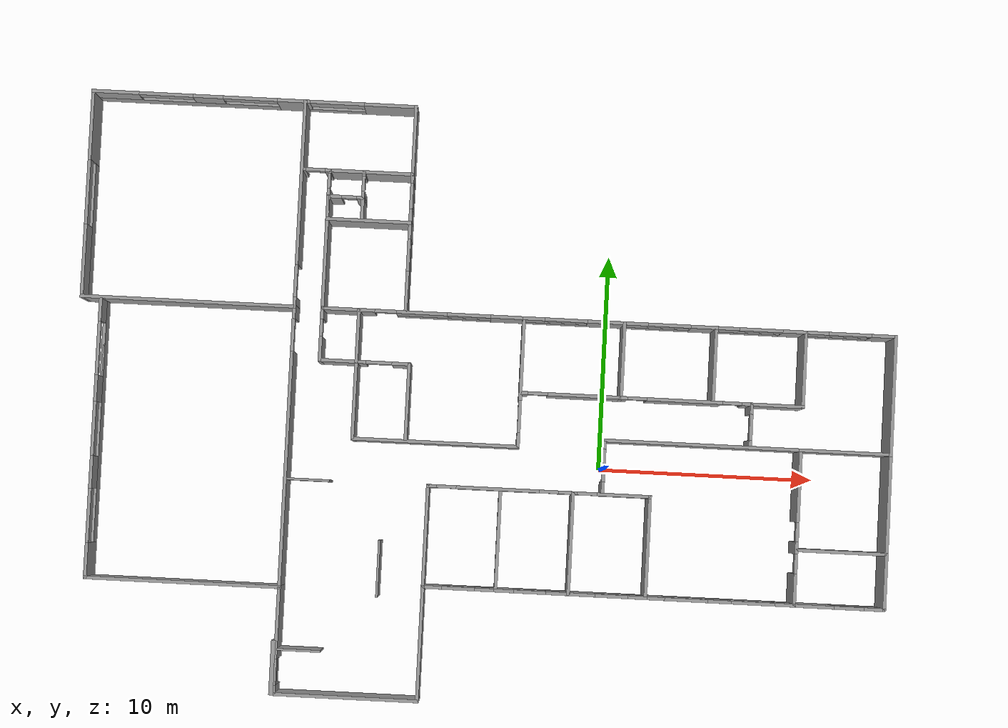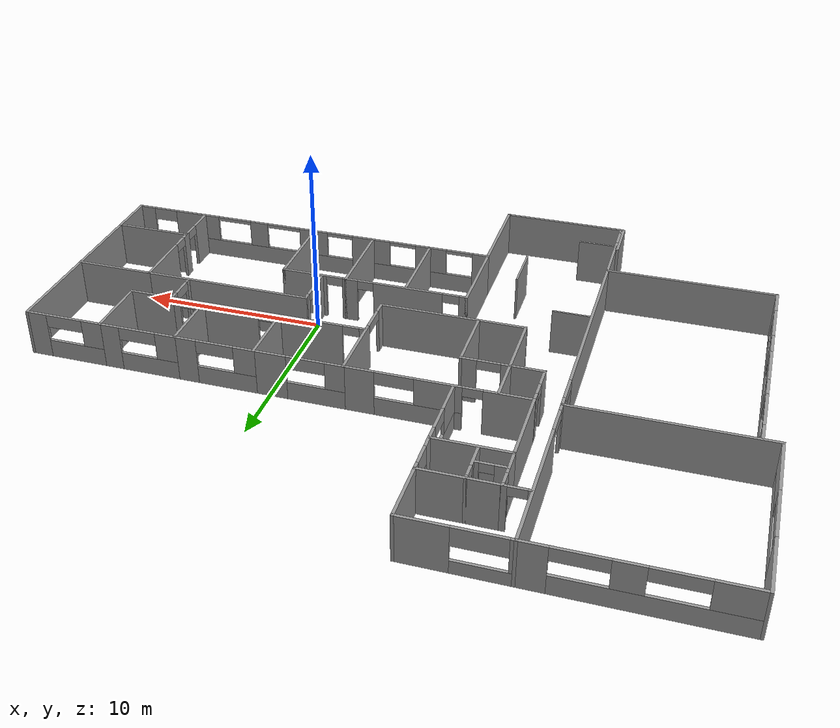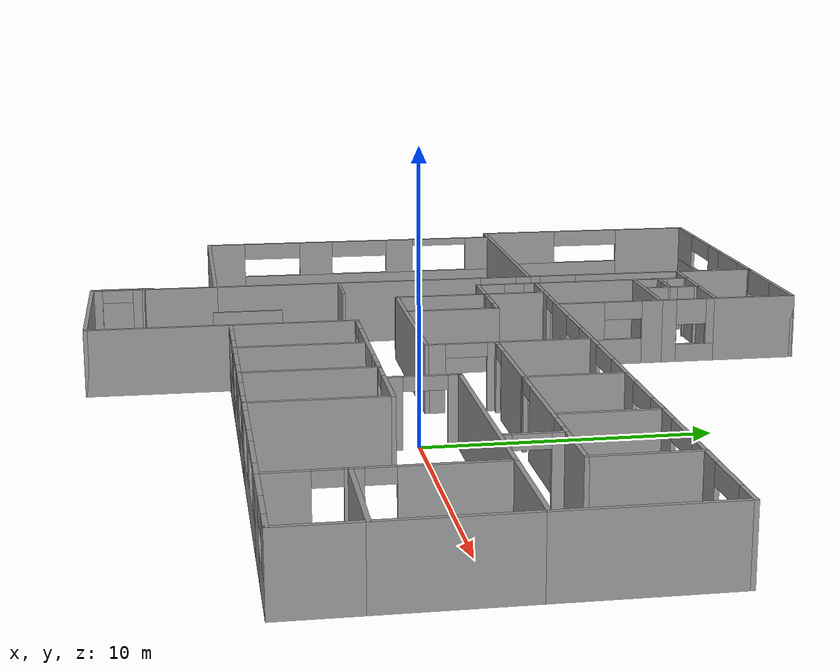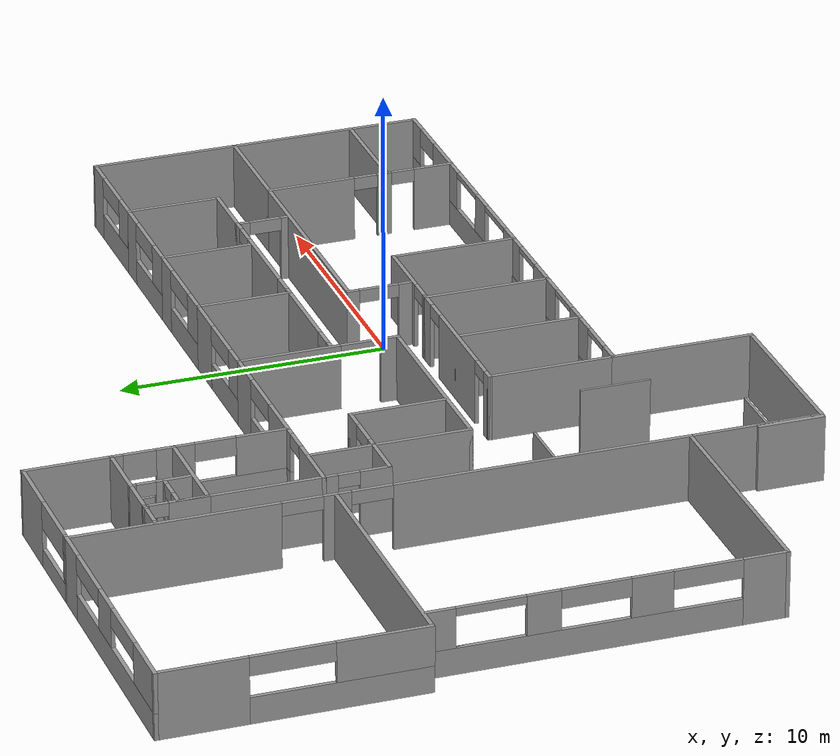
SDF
<?xml version='1.0'?>
<sdf version='1.5'>
  <model name='Centro_Piaggio'>
    <pose>-5.53691 2.63204 0 0 -0 0</pose>
    <link name='Wall_100'>
      <collision name='Wall_100_Collision'>
        <geometry>
          <box>
            <size>6.763 0.15 2.5</size>
          </box>
        </geometry>
        <pose>0 0 1.25 0 -0 0</pose>
      </collision>
      <visual name='Wall_100_Visual'>
        <pose>0 0 1.25 0 -0 0</pose>
        <geometry>
          <box>
            <size>6.763 0.15 2.5</size>
          </box>
        </geometry>
        <material>
          <script>
            <uri>file://media/materials/scripts/gazebo.material</uri>
            <name>Gazebo/Grey</name>
          </script>
        </material>
      </visual>
      <pose>-5.70659 -13.7 0 0 -0 0</pose>
    </link>
    <link name='Wall_102'>
      <collision name='Wall_102_Collision'>
        <geometry>
          <box>
            <size>5.4 0.15 2.5</size>
          </box>
        </geometry>
        <pose>0 0 1.25 0 -0 0</pose>
      </collision>
      <visual name='Wall_102_Visual'>
        <pose>0 0 1.25 0 -0 0</pose>
        <geometry>
          <box>
            <size>5.4 0.15 2.5</size>
          </box>
        </geometry>
        <material>
          <script>
            <uri>file://media/materials/scripts/gazebo.material</uri>
            <name>Gazebo/Grey</name>
          </script>
        </material>
      </visual>
      <pose>-2.40005 -11.075 0 0 -0 1.57078</pose>
    </link>
    <link name='Wall_104'>
      <pose>-0.725 -8.44996 0 0 -0 0</pose>
      <visual name='Wall_104_Visual_0'>
        <pose>-1.275 0 1.25 0 -0 0</pose>
        <geometry>
          <box>
            <size>0.949996 0.15 2.5</size>
          </box>
        </geometry>
        <material>
          <script>
            <uri>file://media/materials/scripts/gazebo.material</uri>
            <name>Gazebo/Grey</name>
          </script>
        </material>
      </visual>
      <collision name='Wall_104_Collision_0'>
        <geometry>
          <box>
            <size>0.949996 0.15 2.5</size>
          </box>
        </geometry>
        <pose>-1.275 0 1.25 0 -0 0</pose>
      </collision>
      <visual name='Wall_104_Visual_1'>
        <pose>0.474998 0 0.5 0 -0 0</pose>
        <geometry>
          <box>
            <size>2.55 0.15 1</size>
          </box>
        </geometry>
        <material>
          <script>
            <uri>file://media/materials/scripts/gazebo.material</uri>
            <name>Gazebo/Grey</name>
          </script>
        </material>
      </visual>
      <collision name='Wall_104_Collision_1'>
        <geometry>
          <box>
            <size>2.55 0.15 1</size>
          </box>
        </geometry>
        <pose>0.474998 0 0.5 0 -0 0</pose>
      </collision>
      <visual name='Wall_104_Visual_2'>
        <pose>1.225 0 1.75 0 -0 0</pose>
        <geometry>
          <box>
            <size>1.05 0.15 1.5</size>
          </box>
        </geometry>
        <material>
          <script>
            <uri>file://media/materials/scripts/gazebo.material</uri>
            <name>Gazebo/Grey</name>
          </script>
        </material>
      </visual>
      <collision name='Wall_104_Collision_2'>
        <geometry>
          <box>
            <size>1.05 0.15 1.5</size>
          </box>
        </geometry>
        <pose>1.225 0 1.75 0 -0 0</pose>
      </collision>
      <visual name='Wall_104_Visual_3'>
        <pose>-0.050004 0 2.4 0 -0 0</pose>
        <geometry>
          <box>
            <size>1.5 0.15 0.2</size>
          </box>
        </geometry>
        <material>
          <script>
            <uri>file://media/materials/scripts/gazebo.material</uri>
            <name>Gazebo/Grey</name>
          </script>
        </material>
      </visual>
      <collision name='Wall_104_Collision_3'>
        <geometry>
          <box>
            <size>1.5 0.15 0.2</size>
          </box>
        </geometry>
        <pose>-0.050004 0 2.4 0 -0 0</pose>
      </collision>
    </link>
    <link name='Wall_110'>
      <collision name='Wall_110_Collision'>
        <geometry>
          <box>
            <size>4.8 0.15 2.5</size>
          </box>
        </geometry>
        <pose>0 0 1.25 0 -0 0</pose>
      </collision>
      <visual name='Wall_110_Visual'>
        <pose>0 0 1.25 0 -0 0</pose>
        <geometry>
          <box>
            <size>4.8 0.15 2.5</size>
          </box>
        </geometry>
        <material>
          <script>
            <uri>file://media/materials/scripts/gazebo.material</uri>
            <name>Gazebo/Grey</name>
          </script>
        </material>
      </visual>
      <pose>-2.4 -6.12496 0 0 -0 1.5708</pose>
    </link>
    <link name='Wall_113'>
      <collision name='Wall_113_Collision'>
        <geometry>
          <box>
            <size>4.8 0.15 2.5</size>
          </box>
        </geometry>
        <pose>0 0 1.25 0 -0 0</pose>
      </collision>
      <visual name='Wall_113_Visual'>
        <pose>0 0 1.25 0 -0 0</pose>
        <geometry>
          <box>
            <size>4.8 0.15 2.5</size>
          </box>
        </geometry>
        <material>
          <script>
            <uri>file://media/materials/scripts/gazebo.material</uri>
            <name>Gazebo/Grey</name>
          </script>
        </material>
      </visual>
      <pose>0.95 -6.12496 0 0 -0 1.5708</pose>
    </link>
    <link name='Wall_115'>
      <pose>2.625 -8.44996 0 0 -0 0</pose>
      <visual name='Wall_115_Visual_0'>
        <pose>-1.2984 0 1.25 0 -0 0</pose>
        <geometry>
          <box>
            <size>0.903193 0.15 2.5</size>
          </box>
        </geometry>
        <material>
          <script>
            <uri>file://media/materials/scripts/gazebo.material</uri>
            <name>Gazebo/Grey</name>
          </script>
        </material>
      </visual>
      <collision name='Wall_115_Collision_0'>
        <geometry>
          <box>
            <size>0.903193 0.15 2.5</size>
          </box>
        </geometry>
        <pose>-1.2984 0 1.25 0 -0 0</pose>
      </collision>
      <visual name='Wall_115_Visual_1'>
        <pose>0.451597 0 0.5 0 -0 0</pose>
        <geometry>
          <box>
            <size>2.59681 0.15 1</size>
          </box>
        </geometry>
        <material>
          <script>
            <uri>file://media/materials/scripts/gazebo.material</uri>
            <name>Gazebo/Grey</name>
          </script>
        </material>
      </visual>
      <collision name='Wall_115_Collision_1'>
        <geometry>
          <box>
            <size>2.59681 0.15 1</size>
          </box>
        </geometry>
        <pose>0.451597 0 0.5 0 -0 0</pose>
      </collision>
      <visual name='Wall_115_Visual_2'>
        <pose>1.2016 0 1.75 0 -0 0</pose>
        <geometry>
          <box>
            <size>1.09681 0.15 1.5</size>
          </box>
        </geometry>
        <material>
          <script>
            <uri>file://media/materials/scripts/gazebo.material</uri>
            <name>Gazebo/Grey</name>
          </script>
        </material>
      </visual>
      <collision name='Wall_115_Collision_2'>
        <geometry>
          <box>
            <size>1.09681 0.15 1.5</size>
          </box>
        </geometry>
        <pose>1.2016 0 1.75 0 -0 0</pose>
      </collision>
      <visual name='Wall_115_Visual_3'>
        <pose>-0.096807 0 2.4 0 -0 0</pose>
        <geometry>
          <box>
            <size>1.5 0.15 0.2</size>
          </box>
        </geometry>
        <material>
          <script>
            <uri>file://media/materials/scripts/gazebo.material</uri>
            <name>Gazebo/Grey</name>
          </script>
        </material>
      </visual>
      <collision name='Wall_115_Collision_3'>
        <geometry>
          <box>
            <size>1.5 0.15 0.2</size>
          </box>
        </geometry>
        <pose>-0.096807 0 2.4 0 -0 0</pose>
      </collision>
    </link>
    <link name='Wall_119'>
      <collision name='Wall_119_Collision'>
        <geometry>
          <box>
            <size>4.8 0.15 2.5</size>
          </box>
        </geometry>
        <pose>0 0 1.25 0 -0 0</pose>
      </collision>
      <visual name='Wall_119_Visual'>
        <pose>0 0 1.25 0 -0 0</pose>
        <geometry>
          <box>
            <size>4.8 0.15 2.5</size>
          </box>
        </geometry>
        <material>
          <script>
            <uri>file://media/materials/scripts/gazebo.material</uri>
            <name>Gazebo/Grey</name>
          </script>
        </material>
      </visual>
      <pose>4.3 -6.12496 0 0 -0 1.5708</pose>
    </link>
    <link name='Wall_121'>
      <pose>6.075 -8.44996 0 0 -0 0</pose>
      <visual name='Wall_121_Visual_0'>
        <pose>-1.18918 0 1.25 0 -0 0</pose>
        <geometry>
          <box>
            <size>1.32163 0.15 2.5</size>
          </box>
        </geometry>
        <material>
          <script>
            <uri>file://media/materials/scripts/gazebo.material</uri>
            <name>Gazebo/Grey</name>
          </script>
        </material>
      </visual>
      <collision name='Wall_121_Collision_0'>
        <geometry>
          <box>
            <size>1.32163 0.15 2.5</size>
          </box>
        </geometry>
        <pose>-1.18918 0 1.25 0 -0 0</pose>
      </collision>
      <visual name='Wall_121_Visual_1'>
        <pose>0.660815 0 0.5 0 -0 0</pose>
        <geometry>
          <box>
            <size>2.37837 0.15 1</size>
          </box>
        </geometry>
        <material>
          <script>
            <uri>file://media/materials/scripts/gazebo.material</uri>
            <name>Gazebo/Grey</name>
          </script>
        </material>
      </visual>
      <collision name='Wall_121_Collision_1'>
        <geometry>
          <box>
            <size>2.37837 0.15 1</size>
          </box>
        </geometry>
        <pose>0.660815 0 0.5 0 -0 0</pose>
      </collision>
      <visual name='Wall_121_Visual_2'>
        <pose>1.41081 0 1.75 0 -0 0</pose>
        <geometry>
          <box>
            <size>0.878369 0.15 1.5</size>
          </box>
        </geometry>
        <material>
          <script>
            <uri>file://media/materials/scripts/gazebo.material</uri>
            <name>Gazebo/Grey</name>
          </script>
        </material>
      </visual>
      <collision name='Wall_121_Collision_2'>
        <geometry>
          <box>
            <size>0.878369 0.15 1.5</size>
          </box>
        </geometry>
        <pose>1.41081 0 1.75 0 -0 0</pose>
      </collision>
      <visual name='Wall_121_Visual_3'>
        <pose>0.221631 0 2.4 0 -0 0</pose>
        <geometry>
          <box>
            <size>1.5 0.15 0.2</size>
          </box>
        </geometry>
        <material>
          <script>
            <uri>file://media/materials/scripts/gazebo.material</uri>
            <name>Gazebo/Grey</name>
          </script>
        </material>
      </visual>
      <collision name='Wall_121_Collision_3'>
        <geometry>
          <box>
            <size>1.5 0.15 0.2</size>
          </box>
        </geometry>
        <pose>0.221631 0 2.4 0 -0 0</pose>
      </collision>
    </link>
    <link name='Wall_123'>
      <collision name='Wall_123_Collision'>
        <geometry>
          <box>
            <size>4.8 0.15 2.5</size>
          </box>
        </geometry>
        <pose>0 0 1.25 0 -0 0</pose>
      </collision>
      <visual name='Wall_123_Visual'>
        <pose>0 0 1.25 0 -0 0</pose>
        <geometry>
          <box>
            <size>4.8 0.15 2.5</size>
          </box>
        </geometry>
        <material>
          <script>
            <uri>file://media/materials/scripts/gazebo.material</uri>
            <name>Gazebo/Grey</name>
          </script>
        </material>
      </visual>
      <pose>7.85 -6.12496 0 0 -0 1.5708</pose>
    </link>
    <link name='Wall_125'>
      <pose>2.725 -3.79996 0 0 -0 0</pose>
      <visual name='Wall_125_Visual_0'>
        <pose>-4.96091 0 1.25 0 -0 0</pose>
        <geometry>
          <box>
            <size>0.478182 0.15 2.5</size>
          </box>
        </geometry>
        <material>
          <script>
            <uri>file://media/materials/scripts/gazebo.material</uri>
            <name>Gazebo/Grey</name>
          </script>
        </material>
      </visual>
      <collision name='Wall_125_Collision_0'>
        <geometry>
          <box>
            <size>0.478182 0.15 2.5</size>
          </box>
        </geometry>
        <pose>-4.96091 0 1.25 0 -0 0</pose>
      </collision>
      <visual name='Wall_125_Visual_1'>
        <pose>-1.9044 0 1.25 0 -0 0</pose>
        <geometry>
          <box>
            <size>3.83483 0.15 2.5</size>
          </box>
        </geometry>
        <material>
          <script>
            <uri>file://media/materials/scripts/gazebo.material</uri>
            <name>Gazebo/Grey</name>
          </script>
        </material>
      </visual>
      <collision name='Wall_125_Collision_1'>
        <geometry>
          <box>
            <size>3.83483 0.15 2.5</size>
          </box>
        </geometry>
        <pose>-1.9044 0 1.25 0 -0 0</pose>
      </collision>
      <visual name='Wall_125_Visual_2'>
        <pose>1.34082 0 1.25 0 -0 0</pose>
        <geometry>
          <box>
            <size>0.855613 0.15 2.5</size>
          </box>
        </geometry>
        <material>
          <script>
            <uri>file://media/materials/scripts/gazebo.material</uri>
            <name>Gazebo/Grey</name>
          </script>
        </material>
      </visual>
      <collision name='Wall_125_Collision_2'>
        <geometry>
          <box>
            <size>0.855613 0.15 2.5</size>
          </box>
        </geometry>
        <pose>1.34082 0 1.25 0 -0 0</pose>
      </collision>
      <visual name='Wall_125_Visual_3'>
        <pose>3.93431 0 1.25 0 -0 0</pose>
        <geometry>
          <box>
            <size>2.53137 0.15 2.5</size>
          </box>
        </geometry>
        <material>
          <script>
            <uri>file://media/materials/scripts/gazebo.material</uri>
            <name>Gazebo/Grey</name>
          </script>
        </material>
      </visual>
      <collision name='Wall_125_Collision_3'>
        <geometry>
          <box>
            <size>2.53137 0.15 2.5</size>
          </box>
        </geometry>
        <pose>3.93431 0 1.25 0 -0 0</pose>
      </collision>
      <visual name='Wall_125_Visual_4'>
        <pose>-4.27182 0 2.25 0 -0 0</pose>
        <geometry>
          <box>
            <size>0.9 0.15 0.5</size>
          </box>
        </geometry>
        <material>
          <script>
            <uri>file://media/materials/scripts/gazebo.material</uri>
            <name>Gazebo/Grey</name>
          </script>
        </material>
      </visual>
      <collision name='Wall_125_Collision_4'>
        <geometry>
          <box>
            <size>0.9 0.15 0.5</size>
          </box>
        </geometry>
        <pose>-4.27182 0 2.25 0 -0 0</pose>
      </collision>
      <visual name='Wall_125_Visual_5'>
        <pose>0.463017 0 2.25 0 -0 0</pose>
        <geometry>
          <box>
            <size>0.9 0.15 0.5</size>
          </box>
        </geometry>
        <material>
          <script>
            <uri>file://media/materials/scripts/gazebo.material</uri>
            <name>Gazebo/Grey</name>
          </script>
        </material>
      </visual>
      <collision name='Wall_125_Collision_5'>
        <geometry>
          <box>
            <size>0.9 0.15 0.5</size>
          </box>
        </geometry>
        <pose>0.463017 0 2.25 0 -0 0</pose>
      </collision>
      <visual name='Wall_125_Visual_6'>
        <pose>2.21863 0 2.25 0 -0 0</pose>
        <geometry>
          <box>
            <size>0.9 0.15 0.5</size>
          </box>
        </geometry>
        <material>
          <script>
            <uri>file://media/materials/scripts/gazebo.material</uri>
            <name>Gazebo/Grey</name>
          </script>
        </material>
      </visual>
      <collision name='Wall_125_Collision_6'>
        <geometry>
          <box>
            <size>0.9 0.15 0.5</size>
          </box>
        </geometry>
        <pose>2.21863 0 2.25 0 -0 0</pose>
      </collision>
    </link>
    <link name='Wall_127'>
      <pose>11.275 -8.44996 0 0 -0 0</pose>
      <visual name='Wall_127_Visual_0'>
        <pose>-3.0178 0 1.25 0 -0 0</pose>
        <geometry>
          <box>
            <size>0.9644 0.15 2.5</size>
          </box>
        </geometry>
        <material>
          <script>
            <uri>file://media/materials/scripts/gazebo.material</uri>
            <name>Gazebo/Grey</name>
          </script>
        </material>
      </visual>
      <collision name='Wall_127_Collision_0'>
        <geometry>
          <box>
            <size>0.9644 0.15 2.5</size>
          </box>
        </geometry>
        <pose>-3.0178 0 1.25 0 -0 0</pose>
      </collision>
      <visual name='Wall_127_Visual_1'>
        <pose>0.4822 0 0.5 0 -0 0</pose>
        <geometry>
          <box>
            <size>6.0356 0.15 1</size>
          </box>
        </geometry>
        <material>
          <script>
            <uri>file://media/materials/scripts/gazebo.material</uri>
            <name>Gazebo/Grey</name>
          </script>
        </material>
      </visual>
      <collision name='Wall_127_Collision_1'>
        <geometry>
          <box>
            <size>6.0356 0.15 1</size>
          </box>
        </geometry>
        <pose>0.4822 0 0.5 0 -0 0</pose>
      </collision>
      <visual name='Wall_127_Visual_2'>
        <pose>-0.000311 0 1.75 0 -0 0</pose>
        <geometry>
          <box>
            <size>1.07058 0.15 1.5</size>
          </box>
        </geometry>
        <material>
          <script>
            <uri>file://media/materials/scripts/gazebo.material</uri>
            <name>Gazebo/Grey</name>
          </script>
        </material>
      </visual>
      <collision name='Wall_127_Collision_2'>
        <geometry>
          <box>
            <size>1.07058 0.15 1.5</size>
          </box>
        </geometry>
        <pose>-0.000311 0 1.75 0 -0 0</pose>
      </collision>
      <visual name='Wall_127_Visual_3'>
        <pose>3.01749 0 1.75 0 -0 0</pose>
        <geometry>
          <box>
            <size>0.965022 0.15 1.5</size>
          </box>
        </geometry>
        <material>
          <script>
            <uri>file://media/materials/scripts/gazebo.material</uri>
            <name>Gazebo/Grey</name>
          </script>
        </material>
      </visual>
      <collision name='Wall_127_Collision_3'>
        <geometry>
          <box>
            <size>0.965022 0.15 1.5</size>
          </box>
        </geometry>
        <pose>3.01749 0 1.75 0 -0 0</pose>
      </collision>
      <visual name='Wall_127_Visual_4'>
        <pose>-1.5356 0 2.4 0 -0 0</pose>
        <geometry>
          <box>
            <size>2 0.15 0.2</size>
          </box>
        </geometry>
        <material>
          <script>
            <uri>file://media/materials/scripts/gazebo.material</uri>
            <name>Gazebo/Grey</name>
          </script>
        </material>
      </visual>
      <collision name='Wall_127_Collision_4'>
        <geometry>
          <box>
            <size>2 0.15 0.2</size>
          </box>
        </geometry>
        <pose>-1.5356 0 2.4 0 -0 0</pose>
      </collision>
      <visual name='Wall_127_Visual_5'>
        <pose>1.53498 0 2.4 0 -0 0</pose>
        <geometry>
          <box>
            <size>2 0.15 0.2</size>
          </box>
        </geometry>
        <material>
          <script>
            <uri>file://media/materials/scripts/gazebo.material</uri>
            <name>Gazebo/Grey</name>
          </script>
        </material>
      </visual>
      <collision name='Wall_127_Collision_5'>
        <geometry>
          <box>
            <size>2 0.15 0.2</size>
          </box>
        </geometry>
        <pose>1.53498 0 2.4 0 -0 0</pose>
      </collision>
    </link>
    <link name='Wall_129'>
      <pose>14.7 -4.87496 0 0 -0 1.5708</pose>
      <visual name='Wall_129_Visual_0'>
        <pose>-2.87687 0 1.25 0 -0 0</pose>
        <geometry>
          <box>
            <size>1.54626 0.15 2.5</size>
          </box>
        </geometry>
        <material>
          <script>
            <uri>file://media/materials/scripts/gazebo.material</uri>
            <name>Gazebo/Grey</name>
          </script>
        </material>
      </visual>
      <collision name='Wall_129_Collision_0'>
        <geometry>
          <box>
            <size>1.54626 0.15 2.5</size>
          </box>
        </geometry>
        <pose>-2.87687 0 1.25 0 -0 0</pose>
      </collision>
      <visual name='Wall_129_Visual_1'>
        <pose>-0.922239 0 1.25 0 -0 0</pose>
        <geometry>
          <box>
            <size>0.563011 0.15 2.5</size>
          </box>
        </geometry>
        <material>
          <script>
            <uri>file://media/materials/scripts/gazebo.material</uri>
            <name>Gazebo/Grey</name>
          </script>
        </material>
      </visual>
      <collision name='Wall_129_Collision_1'>
        <geometry>
          <box>
            <size>0.563011 0.15 2.5</size>
          </box>
        </geometry>
        <pose>-0.922239 0 1.25 0 -0 0</pose>
      </collision>
      <visual name='Wall_129_Visual_2'>
        <pose>1.95463 0 1.25 0 -0 0</pose>
        <geometry>
          <box>
            <size>3.39073 0.15 2.5</size>
          </box>
        </geometry>
        <material>
          <script>
            <uri>file://media/materials/scripts/gazebo.material</uri>
            <name>Gazebo/Grey</name>
          </script>
        </material>
      </visual>
      <collision name='Wall_129_Collision_2'>
        <geometry>
          <box>
            <size>3.39073 0.15 2.5</size>
          </box>
        </geometry>
        <pose>1.95463 0 1.25 0 -0 0</pose>
      </collision>
      <visual name='Wall_129_Visual_3'>
        <pose>-1.65374 0 2.25 0 -0 0</pose>
        <geometry>
          <box>
            <size>0.9 0.15 0.5</size>
          </box>
        </geometry>
        <material>
          <script>
            <uri>file://media/materials/scripts/gazebo.material</uri>
            <name>Gazebo/Grey</name>
          </script>
        </material>
      </visual>
      <collision name='Wall_129_Collision_3'>
        <geometry>
          <box>
            <size>0.9 0.15 0.5</size>
          </box>
        </geometry>
        <pose>-1.65374 0 2.25 0 -0 0</pose>
      </collision>
      <visual name='Wall_129_Visual_4'>
        <pose>-0.190733 0 2.25 0 -0 0</pose>
        <geometry>
          <box>
            <size>0.9 0.15 0.5</size>
          </box>
        </geometry>
        <material>
          <script>
            <uri>file://media/materials/scripts/gazebo.material</uri>
            <name>Gazebo/Grey</name>
          </script>
        </material>
      </visual>
      <collision name='Wall_129_Collision_4'>
        <geometry>
          <box>
            <size>0.9 0.15 0.5</size>
          </box>
        </geometry>
        <pose>-0.190733 0 2.25 0 -0 0</pose>
      </collision>
    </link>
    <link name='Wall_131'>
      <pose>16.775 -8.44996 0 0 -0 0</pose>
      <visual name='Wall_131_Visual_0'>
        <pose>-1.19762 0 1.25 0 -0 0</pose>
        <geometry>
          <box>
            <size>1.90475 0.15 2.5</size>
          </box>
        </geometry>
        <material>
          <script>
            <uri>file://media/materials/scripts/gazebo.material</uri>
            <name>Gazebo/Grey</name>
          </script>
        </material>
      </visual>
      <collision name='Wall_131_Collision_0'>
        <geometry>
          <box>
            <size>1.90475 0.15 2.5</size>
          </box>
        </geometry>
        <pose>-1.19762 0 1.25 0 -0 0</pose>
      </collision>
      <visual name='Wall_131_Visual_1'>
        <pose>0.952375 0 0.5 0 -0 0</pose>
        <geometry>
          <box>
            <size>2.39525 0.15 1</size>
          </box>
        </geometry>
        <material>
          <script>
            <uri>file://media/materials/scripts/gazebo.material</uri>
            <name>Gazebo/Grey</name>
          </script>
        </material>
      </visual>
      <collision name='Wall_131_Collision_1'>
        <geometry>
          <box>
            <size>2.39525 0.15 1</size>
          </box>
        </geometry>
        <pose>0.952375 0 0.5 0 -0 0</pose>
      </collision>
      <visual name='Wall_131_Visual_2'>
        <pose>1.65237 0 1.75 0 -0 0</pose>
        <geometry>
          <box>
            <size>0.99525 0.15 1.5</size>
          </box>
        </geometry>
        <material>
          <script>
            <uri>file://media/materials/scripts/gazebo.material</uri>
            <name>Gazebo/Grey</name>
          </script>
        </material>
      </visual>
      <collision name='Wall_131_Collision_2'>
        <geometry>
          <box>
            <size>0.99525 0.15 1.5</size>
          </box>
        </geometry>
        <pose>1.65237 0 1.75 0 -0 0</pose>
      </collision>
      <visual name='Wall_131_Visual_3'>
        <pose>0.45475 0 2.15 0 -0 0</pose>
        <geometry>
          <box>
            <size>1.4 0.15 0.7</size>
          </box>
        </geometry>
        <material>
          <script>
            <uri>file://media/materials/scripts/gazebo.material</uri>
            <name>Gazebo/Grey</name>
          </script>
        </material>
      </visual>
      <collision name='Wall_131_Collision_3'>
        <geometry>
          <box>
            <size>1.4 0.15 0.7</size>
          </box>
        </geometry>
        <pose>0.45475 0 2.15 0 -0 0</pose>
      </collision>
    </link>
    <link name='Wall_133'>
      <collision name='Wall_133_Collision'>
        <geometry>
          <box>
            <size>2.7 0.15 2.5</size>
          </box>
        </geometry>
        <pose>0 0 1.25 0 -0 0</pose>
      </collision>
      <visual name='Wall_133_Visual'>
        <pose>0 0 1.25 0 -0 0</pose>
        <geometry>
          <box>
            <size>2.7 0.15 2.5</size>
          </box>
        </geometry>
        <material>
          <script>
            <uri>file://media/materials/scripts/gazebo.material</uri>
            <name>Gazebo/Grey</name>
          </script>
        </material>
      </visual>
      <pose>18.85 -7.17496 0 0 -0 1.5708</pose>
    </link>
    <link name='Wall_135'>
      <collision name='Wall_135_Collision'>
        <geometry>
          <box>
            <size>4.25 0.15 2.5</size>
          </box>
        </geometry>
        <pose>0 0 1.25 0 -0 0</pose>
      </collision>
      <visual name='Wall_135_Visual'>
        <pose>0 0 1.25 0 -0 0</pose>
        <geometry>
          <box>
            <size>4.25 0.15 2.5</size>
          </box>
        </geometry>
        <material>
          <script>
            <uri>file://media/materials/scripts/gazebo.material</uri>
            <name>Gazebo/Grey</name>
          </script>
        </material>
      </visual>
      <pose>16.8 -5.89996 0 0 -0 3.14159</pose>
    </link>
    <link name='Wall_140'>
      <collision name='Wall_140_Collision'>
        <geometry>
          <box>
            <size>4.3 0.15 2.5</size>
          </box>
        </geometry>
        <pose>0 0 1.25 0 -0 0</pose>
      </collision>
      <visual name='Wall_140_Visual'>
        <pose>0 0 1.25 0 -0 0</pose>
        <geometry>
          <box>
            <size>4.3 0.15 2.5</size>
          </box>
        </geometry>
        <material>
          <script>
            <uri>file://media/materials/scripts/gazebo.material</uri>
            <name>Gazebo/Grey</name>
          </script>
        </material>
      </visual>
      <pose>16.775 -1.29996 0 0 -0 0</pose>
    </link>
    <link name='Wall_142'>
      <collision name='Wall_142_Collision'>
        <geometry>
          <box>
            <size>4.75 0.15 2.5</size>
          </box>
        </geometry>
        <pose>0 0 1.25 0 -0 0</pose>
      </collision>
      <visual name='Wall_142_Visual'>
        <pose>0 0 1.25 0 -0 0</pose>
        <geometry>
          <box>
            <size>4.75 0.15 2.5</size>
          </box>
        </geometry>
        <material>
          <script>
            <uri>file://media/materials/scripts/gazebo.material</uri>
            <name>Gazebo/Grey</name>
          </script>
        </material>
      </visual>
      <pose>18.85 -3.59996 0 0 -0 1.5708</pose>
    </link>
    <link name='Wall_144'>
      <collision name='Wall_144_Collision'>
        <geometry>
          <box>
            <size>9.2 0.15 2.5</size>
          </box>
        </geometry>
        <pose>0 0 1.25 0 -0 0</pose>
      </collision>
      <visual name='Wall_144_Visual'>
        <pose>0 0 1.25 0 -0 0</pose>
        <geometry>
          <box>
            <size>9.2 0.15 2.5</size>
          </box>
        </geometry>
        <material>
          <script>
            <uri>file://media/materials/scripts/gazebo.material</uri>
            <name>Gazebo/Grey</name>
          </script>
        </material>
      </visual>
      <pose>10.175 -1.29996 0 0 -0 3.14159</pose>
    </link>
    <link name='Wall_146'>
      <pose>5.65 -2.47496 0 0 0 -1.5708</pose>
      <visual name='Wall_146_Visual_0'>
        <pose>-1.00804 0 1.25 0 -0 0</pose>
        <geometry>
          <box>
            <size>0.483914 0.15 2.5</size>
          </box>
        </geometry>
        <material>
          <script>
            <uri>file://media/materials/scripts/gazebo.material</uri>
            <name>Gazebo/Grey</name>
          </script>
        </material>
      </visual>
      <collision name='Wall_146_Collision_0'>
        <geometry>
          <box>
            <size>0.483914 0.15 2.5</size>
          </box>
        </geometry>
        <pose>-1.00804 0 1.25 0 -0 0</pose>
      </collision>
      <visual name='Wall_146_Visual_1'>
        <pose>0.991957 0 1.25 0 -0 0</pose>
        <geometry>
          <box>
            <size>0.516086 0.15 2.5</size>
          </box>
        </geometry>
        <material>
          <script>
            <uri>file://media/materials/scripts/gazebo.material</uri>
            <name>Gazebo/Grey</name>
          </script>
        </material>
      </visual>
      <collision name='Wall_146_Collision_1'>
        <geometry>
          <box>
            <size>0.516086 0.15 2.5</size>
          </box>
        </geometry>
        <pose>0.991957 0 1.25 0 -0 0</pose>
      </collision>
      <visual name='Wall_146_Visual_2'>
        <pose>-0.016086 0 2.25 0 -0 0</pose>
        <geometry>
          <box>
            <size>1.5 0.15 0.5</size>
          </box>
        </geometry>
        <material>
          <script>
            <uri>file://media/materials/scripts/gazebo.material</uri>
            <name>Gazebo/Grey</name>
          </script>
        </material>
      </visual>
      <collision name='Wall_146_Collision_2'>
        <geometry>
          <box>
            <size>1.5 0.15 0.5</size>
          </box>
        </geometry>
        <pose>-0.016086 0 2.25 0 -0 0</pose>
      </collision>
    </link>
    <link name='Wall_148'>
      <collision name='Wall_148_Collision'>
        <geometry>
          <box>
            <size>5.6 0.15 2.5</size>
          </box>
        </geometry>
        <pose>0 0 1.25 0 -0 0</pose>
      </collision>
      <visual name='Wall_148_Visual'>
        <pose>0 0 1.25 0 -0 0</pose>
        <geometry>
          <box>
            <size>5.6 0.15 2.5</size>
          </box>
        </geometry>
        <material>
          <script>
            <uri>file://media/materials/scripts/gazebo.material</uri>
            <name>Gazebo/Grey</name>
          </script>
        </material>
      </visual>
      <pose>18.85 1.42504 0 0 -0 1.5708</pose>
    </link>
    <link name='Wall_150'>
      <pose>16.775 4.15004 0 0 -0 3.14159</pose>
      <visual name='Wall_150_Visual_0'>
        <pose>-1.55853 0 1.25 0 -0 0</pose>
        <geometry>
          <box>
            <size>1.18295 0.15 2.5</size>
          </box>
        </geometry>
        <material>
          <script>
            <uri>file://media/materials/scripts/gazebo.material</uri>
            <name>Gazebo/Grey</name>
          </script>
        </material>
      </visual>
      <collision name='Wall_150_Collision_0'>
        <geometry>
          <box>
            <size>1.18295 0.15 2.5</size>
          </box>
        </geometry>
        <pose>-1.55853 0 1.25 0 -0 0</pose>
      </collision>
      <visual name='Wall_150_Visual_1'>
        <pose>0.591474 0 0.5 0 -0 0</pose>
        <geometry>
          <box>
            <size>3.11705 0.15 1</size>
          </box>
        </geometry>
        <material>
          <script>
            <uri>file://media/materials/scripts/gazebo.material</uri>
            <name>Gazebo/Grey</name>
          </script>
        </material>
      </visual>
      <collision name='Wall_150_Collision_1'>
        <geometry>
          <box>
            <size>3.11705 0.15 1</size>
          </box>
        </geometry>
        <pose>0.591474 0 0.5 0 -0 0</pose>
      </collision>
      <visual name='Wall_150_Visual_2'>
        <pose>1.59147 0 1.75 0 -0 0</pose>
        <geometry>
          <box>
            <size>1.11705 0.15 1.5</size>
          </box>
        </geometry>
        <material>
          <script>
            <uri>file://media/materials/scripts/gazebo.material</uri>
            <name>Gazebo/Grey</name>
          </script>
        </material>
      </visual>
      <collision name='Wall_150_Collision_2'>
        <geometry>
          <box>
            <size>1.11705 0.15 1.5</size>
          </box>
        </geometry>
        <pose>1.59147 0 1.75 0 -0 0</pose>
      </collision>
      <visual name='Wall_150_Visual_3'>
        <pose>0.032948 0 2.15 0 -0 0</pose>
        <geometry>
          <box>
            <size>2 0.15 0.7</size>
          </box>
        </geometry>
        <material>
          <script>
            <uri>file://media/materials/scripts/gazebo.material</uri>
            <name>Gazebo/Grey</name>
          </script>
        </material>
      </visual>
      <collision name='Wall_150_Collision_3'>
        <geometry>
          <box>
            <size>2 0.15 0.7</size>
          </box>
        </geometry>
        <pose>0.032948 0 2.15 0 -0 0</pose>
      </collision>
    </link>
    <link name='Wall_152'>
      <collision name='Wall_152_Collision'>
        <geometry>
          <box>
            <size>3.6 0.15 2.5</size>
          </box>
        </geometry>
        <pose>0 0 1.25 0 -0 0</pose>
      </collision>
      <visual name='Wall_152_Visual'>
        <pose>0 0 1.25 0 -0 0</pose>
        <geometry>
          <box>
            <size>3.6 0.15 2.5</size>
          </box>
        </geometry>
        <material>
          <script>
            <uri>file://media/materials/scripts/gazebo.material</uri>
            <name>Gazebo/Grey</name>
          </script>
        </material>
      </visual>
      <pose>14.7 2.42504 0 0 0 -1.5708</pose>
    </link>
    <link name='Wall_154'>
      <collision name='Wall_154_Collision'>
        <geometry>
          <box>
            <size>2.5 0.15 2.5</size>
          </box>
        </geometry>
        <pose>0 0 1.25 0 -0 0</pose>
      </collision>
      <visual name='Wall_154_Visual'>
        <pose>0 0 1.25 0 -0 0</pose>
        <geometry>
          <box>
            <size>2.5 0.15 2.5</size>
          </box>
        </geometry>
        <material>
          <script>
            <uri>file://media/materials/scripts/gazebo.material</uri>
            <name>Gazebo/Grey</name>
          </script>
        </material>
      </visual>
      <pose>13.525 0.700041 0 0 -0 3.14159</pose>
    </link>
    <link name='Wall_156'>
      <pose>12.625 4.15004 0 0 -0 3.14159</pose>
      <visual name='Wall_156_Visual_0'>
        <pose>-1.57444 0 1.25 0 -0 0</pose>
        <geometry>
          <box>
            <size>1.15112 0.15 2.5</size>
          </box>
        </geometry>
        <material>
          <script>
            <uri>file://media/materials/scripts/gazebo.material</uri>
            <name>Gazebo/Grey</name>
          </script>
        </material>
      </visual>
      <collision name='Wall_156_Collision_0'>
        <geometry>
          <box>
            <size>1.15112 0.15 2.5</size>
          </box>
        </geometry>
        <pose>-1.57444 0 1.25 0 -0 0</pose>
      </collision>
      <visual name='Wall_156_Visual_1'>
        <pose>0.575558 0 0.5 0 -0 0</pose>
        <geometry>
          <box>
            <size>3.14888 0.15 1</size>
          </box>
        </geometry>
        <material>
          <script>
            <uri>file://media/materials/scripts/gazebo.material</uri>
            <name>Gazebo/Grey</name>
          </script>
        </material>
      </visual>
      <collision name='Wall_156_Collision_1'>
        <geometry>
          <box>
            <size>3.14888 0.15 1</size>
          </box>
        </geometry>
        <pose>0.575558 0 0.5 0 -0 0</pose>
      </collision>
      <visual name='Wall_156_Visual_2'>
        <pose>1.57556 0 1.75 0 -0 0</pose>
        <geometry>
          <box>
            <size>1.14888 0.15 1.5</size>
          </box>
        </geometry>
        <material>
          <script>
            <uri>file://media/materials/scripts/gazebo.material</uri>
            <name>Gazebo/Grey</name>
          </script>
        </material>
      </visual>
      <collision name='Wall_156_Collision_2'>
        <geometry>
          <box>
            <size>1.14888 0.15 1.5</size>
          </box>
        </geometry>
        <pose>1.57556 0 1.75 0 -0 0</pose>
      </collision>
      <visual name='Wall_156_Visual_3'>
        <pose>0.001117 0 2.15 0 -0 0</pose>
        <geometry>
          <box>
            <size>2 0.15 0.7</size>
          </box>
        </geometry>
        <material>
          <script>
            <uri>file://media/materials/scripts/gazebo.material</uri>
            <name>Gazebo/Grey</name>
          </script>
        </material>
      </visual>
      <collision name='Wall_156_Collision_3'>
        <geometry>
          <box>
            <size>2 0.15 0.7</size>
          </box>
        </geometry>
        <pose>0.001117 0 2.15 0 -0 0</pose>
      </collision>
    </link>
    <link name='Wall_158'>
      <pose>12.35 -0.224959 0 0 0 -1.5708</pose>
      <visual name='Wall_158_Visual_0'>
        <pose>-0.735712 0 1.25 0 -0 0</pose>
        <geometry>
          <box>
            <size>0.528576 0.15 2.5</size>
          </box>
        </geometry>
        <material>
          <script>
            <uri>file://media/materials/scripts/gazebo.material</uri>
            <name>Gazebo/Grey</name>
          </script>
        </material>
      </visual>
      <collision name='Wall_158_Collision_0'>
        <geometry>
          <box>
            <size>0.528576 0.15 2.5</size>
          </box>
        </geometry>
        <pose>-0.735712 0 1.25 0 -0 0</pose>
      </collision>
      <visual name='Wall_158_Visual_1'>
        <pose>0.864288 0 1.25 0 -0 0</pose>
        <geometry>
          <box>
            <size>0.271424 0.15 2.5</size>
          </box>
        </geometry>
        <material>
          <script>
            <uri>file://media/materials/scripts/gazebo.material</uri>
            <name>Gazebo/Grey</name>
          </script>
        </material>
      </visual>
      <collision name='Wall_158_Collision_1'>
        <geometry>
          <box>
            <size>0.271424 0.15 2.5</size>
          </box>
        </geometry>
        <pose>0.864288 0 1.25 0 -0 0</pose>
      </collision>
      <visual name='Wall_158_Visual_2'>
        <pose>0.128576 0 2.25 0 -0 0</pose>
        <geometry>
          <box>
            <size>1.2 0.15 0.5</size>
          </box>
        </geometry>
        <material>
          <script>
            <uri>file://media/materials/scripts/gazebo.material</uri>
            <name>Gazebo/Grey</name>
          </script>
        </material>
      </visual>
      <collision name='Wall_158_Collision_2'>
        <geometry>
          <box>
            <size>1.2 0.15 0.5</size>
          </box>
        </geometry>
        <pose>0.128576 0 2.25 0 -0 0</pose>
      </collision>
    </link>
    <link name='Wall_160'>
      <collision name='Wall_160_Collision'>
        <geometry>
          <box>
            <size>3.6 0.15 2.5</size>
          </box>
        </geometry>
        <pose>0 0 1.25 0 -0 0</pose>
      </collision>
      <visual name='Wall_160_Visual'>
        <pose>0 0 1.25 0 -0 0</pose>
        <geometry>
          <box>
            <size>3.6 0.15 2.5</size>
          </box>
        </geometry>
        <material>
          <script>
            <uri>file://media/materials/scripts/gazebo.material</uri>
            <name>Gazebo/Grey</name>
          </script>
        </material>
      </visual>
      <pose>10.55 2.42504 0 0 0 -1.5708</pose>
    </link>
    <link name='Wall_162'>
      <pose>8.425 4.15004 0 0 -0 3.14159</pose>
      <visual name='Wall_162_Visual_0'>
        <pose>-1.5826 0 1.25 0 -0 0</pose>
        <geometry>
          <box>
            <size>1.23479 0.15 2.5</size>
          </box>
        </geometry>
        <material>
          <script>
            <uri>file://media/materials/scripts/gazebo.material</uri>
            <name>Gazebo/Grey</name>
          </script>
        </material>
      </visual>
      <collision name='Wall_162_Collision_0'>
        <geometry>
          <box>
            <size>1.23479 0.15 2.5</size>
          </box>
        </geometry>
        <pose>-1.5826 0 1.25 0 -0 0</pose>
      </collision>
      <visual name='Wall_162_Visual_1'>
        <pose>0.617397 0 0.5 0 -0 0</pose>
        <geometry>
          <box>
            <size>3.16521 0.15 1</size>
          </box>
        </geometry>
        <material>
          <script>
            <uri>file://media/materials/scripts/gazebo.material</uri>
            <name>Gazebo/Grey</name>
          </script>
        </material>
      </visual>
      <collision name='Wall_162_Collision_1'>
        <geometry>
          <box>
            <size>3.16521 0.15 1</size>
          </box>
        </geometry>
        <pose>0.617397 0 0.5 0 -0 0</pose>
      </collision>
      <visual name='Wall_162_Visual_2'>
        <pose>1.6174 0 1.75 0 -0 0</pose>
        <geometry>
          <box>
            <size>1.16521 0.15 1.5</size>
          </box>
        </geometry>
        <material>
          <script>
            <uri>file://media/materials/scripts/gazebo.material</uri>
            <name>Gazebo/Grey</name>
          </script>
        </material>
      </visual>
      <collision name='Wall_162_Collision_2'>
        <geometry>
          <box>
            <size>1.16521 0.15 1.5</size>
          </box>
        </geometry>
        <pose>1.6174 0 1.75 0 -0 0</pose>
      </collision>
      <visual name='Wall_162_Visual_3'>
        <pose>0.034793 0 2.15 0 -0 0</pose>
        <geometry>
          <box>
            <size>2 0.15 0.7</size>
          </box>
        </geometry>
        <material>
          <script>
            <uri>file://media/materials/scripts/gazebo.material</uri>
            <name>Gazebo/Grey</name>
          </script>
        </material>
      </visual>
      <collision name='Wall_162_Collision_3'>
        <geometry>
          <box>
            <size>2 0.15 0.7</size>
          </box>
        </geometry>
        <pose>0.034793 0 2.15 0 -0 0</pose>
      </collision>
    </link>
    <link name='Wall_164'>
      <collision name='Wall_164_Collision'>
        <geometry>
          <box>
            <size>3.6 0.15 2.5</size>
          </box>
        </geometry>
        <pose>0 0 1.25 0 -0 0</pose>
      </collision>
      <visual name='Wall_164_Visual'>
        <pose>0 0 1.25 0 -0 0</pose>
        <geometry>
          <box>
            <size>3.6 0.15 2.5</size>
          </box>
        </geometry>
        <material>
          <script>
            <uri>file://media/materials/scripts/gazebo.material</uri>
            <name>Gazebo/Grey</name>
          </script>
        </material>
      </visual>
      <pose>6.3 2.42504 0 0 0 -1.5708</pose>
    </link>
    <link name='Wall_166'>
      <pose>3.975 4.15004 0 0 -0 3.14159</pose>
      <visual name='Wall_166_Visual_0'>
        <pose>-1.51162 0 1.25 0 -0 0</pose>
        <geometry>
          <box>
            <size>1.77676 0.15 2.5</size>
          </box>
        </geometry>
        <material>
          <script>
            <uri>file://media/materials/scripts/gazebo.material</uri>
            <name>Gazebo/Grey</name>
          </script>
        </material>
      </visual>
      <collision name='Wall_166_Collision_0'>
        <geometry>
          <box>
            <size>1.77676 0.15 2.5</size>
          </box>
        </geometry>
        <pose>-1.51162 0 1.25 0 -0 0</pose>
      </collision>
      <visual name='Wall_166_Visual_1'>
        <pose>0.888378 0 0.5 0 -0 0</pose>
        <geometry>
          <box>
            <size>3.02324 0.15 1</size>
          </box>
        </geometry>
        <material>
          <script>
            <uri>file://media/materials/scripts/gazebo.material</uri>
            <name>Gazebo/Grey</name>
          </script>
        </material>
      </visual>
      <collision name='Wall_166_Collision_1'>
        <geometry>
          <box>
            <size>3.02324 0.15 1</size>
          </box>
        </geometry>
        <pose>0.888378 0 0.5 0 -0 0</pose>
      </collision>
      <visual name='Wall_166_Visual_2'>
        <pose>1.88838 0 1.75 0 -0 0</pose>
        <geometry>
          <box>
            <size>1.02324 0.15 1.5</size>
          </box>
        </geometry>
        <material>
          <script>
            <uri>file://media/materials/scripts/gazebo.material</uri>
            <name>Gazebo/Grey</name>
          </script>
        </material>
      </visual>
      <collision name='Wall_166_Collision_2'>
        <geometry>
          <box>
            <size>1.02324 0.15 1.5</size>
          </box>
        </geometry>
        <pose>1.88838 0 1.75 0 -0 0</pose>
      </collision>
      <visual name='Wall_166_Visual_3'>
        <pose>0.376756 0 2.15 0 -0 0</pose>
        <geometry>
          <box>
            <size>2 0.15 0.7</size>
          </box>
        </geometry>
        <material>
          <script>
            <uri>file://media/materials/scripts/gazebo.material</uri>
            <name>Gazebo/Grey</name>
          </script>
        </material>
      </visual>
      <collision name='Wall_166_Collision_3'>
        <geometry>
          <box>
            <size>2 0.15 0.7</size>
          </box>
        </geometry>
        <pose>0.376756 0 2.15 0 -0 0</pose>
      </collision>
    </link>
    <link name='Wall_168'>
      <pose>1.65 1.17504 0 0 0 -1.5708</pose>
      <visual name='Wall_168_Visual_0'>
        <pose>-1.11548 0 1.25 0 -0 0</pose>
        <geometry>
          <box>
            <size>3.86903 0.15 2.5</size>
          </box>
        </geometry>
        <material>
          <script>
            <uri>file://media/materials/scripts/gazebo.material</uri>
            <name>Gazebo/Grey</name>
          </script>
        </material>
      </visual>
      <collision name='Wall_168_Collision_0'>
        <geometry>
          <box>
            <size>3.86903 0.15 2.5</size>
          </box>
        </geometry>
        <pose>-1.11548 0 1.25 0 -0 0</pose>
      </collision>
      <visual name='Wall_168_Visual_1'>
        <pose>2.68452 0 1.25 0 -0 0</pose>
        <geometry>
          <box>
            <size>0.730968 0.15 2.5</size>
          </box>
        </geometry>
        <material>
          <script>
            <uri>file://media/materials/scripts/gazebo.material</uri>
            <name>Gazebo/Grey</name>
          </script>
        </material>
      </visual>
      <collision name='Wall_168_Collision_1'>
        <geometry>
          <box>
            <size>0.730968 0.15 2.5</size>
          </box>
        </geometry>
        <pose>2.68452 0 1.25 0 -0 0</pose>
      </collision>
      <visual name='Wall_168_Visual_2'>
        <pose>1.56903 0 2.25 0 -0 0</pose>
        <geometry>
          <box>
            <size>1.5 0.15 0.5</size>
          </box>
        </geometry>
        <material>
          <script>
            <uri>file://media/materials/scripts/gazebo.material</uri>
            <name>Gazebo/Grey</name>
          </script>
        </material>
      </visual>
      <collision name='Wall_168_Collision_2'>
        <geometry>
          <box>
            <size>1.5 0.15 0.5</size>
          </box>
        </geometry>
        <pose>1.56903 0 2.25 0 -0 0</pose>
      </collision>
    </link>
    <link name='Wall_170'>
      <pose>7.05 0.700041 0 0 -0 3.14159</pose>
      <visual name='Wall_170_Visual_0'>
        <pose>-5.10679 0 1.25 0 -0 0</pose>
        <geometry>
          <box>
            <size>0.536421 0.15 2.5</size>
          </box>
        </geometry>
        <material>
          <script>
            <uri>file://media/materials/scripts/gazebo.material</uri>
            <name>Gazebo/Grey</name>
          </script>
        </material>
      </visual>
      <collision name='Wall_170_Collision_0'>
        <geometry>
          <box>
            <size>0.536421 0.15 2.5</size>
          </box>
        </geometry>
        <pose>-5.10679 0 1.25 0 -0 0</pose>
      </collision>
      <visual name='Wall_170_Visual_1'>
        <pose>-2.19406 0 1.25 0 -0 0</pose>
        <geometry>
          <box>
            <size>3.48903 0.15 2.5</size>
          </box>
        </geometry>
        <material>
          <script>
            <uri>file://media/materials/scripts/gazebo.material</uri>
            <name>Gazebo/Grey</name>
          </script>
        </material>
      </visual>
      <collision name='Wall_170_Collision_1'>
        <geometry>
          <box>
            <size>3.48903 0.15 2.5</size>
          </box>
        </geometry>
        <pose>-2.19406 0 1.25 0 -0 0</pose>
      </collision>
      <visual name='Wall_170_Visual_2'>
        <pose>2.30137 0 1.25 0 -0 0</pose>
        <geometry>
          <box>
            <size>3.70183 0.15 2.5</size>
          </box>
        </geometry>
        <material>
          <script>
            <uri>file://media/materials/scripts/gazebo.material</uri>
            <name>Gazebo/Grey</name>
          </script>
        </material>
      </visual>
      <collision name='Wall_170_Collision_2'>
        <geometry>
          <box>
            <size>3.70183 0.15 2.5</size>
          </box>
        </geometry>
        <pose>2.30137 0 1.25 0 -0 0</pose>
      </collision>
      <visual name='Wall_170_Visual_3'>
        <pose>5.21364 0 1.25 0 -0 0</pose>
        <geometry>
          <box>
            <size>0.322712 0.15 2.5</size>
          </box>
        </geometry>
        <material>
          <script>
            <uri>file://media/materials/scripts/gazebo.material</uri>
            <name>Gazebo/Grey</name>
          </script>
        </material>
      </visual>
      <collision name='Wall_170_Collision_3'>
        <geometry>
          <box>
            <size>0.322712 0.15 2.5</size>
          </box>
        </geometry>
        <pose>5.21364 0 1.25 0 -0 0</pose>
      </collision>
      <visual name='Wall_170_Visual_4'>
        <pose>-4.38858 0 2.25 0 -0 0</pose>
        <geometry>
          <box>
            <size>0.9 0.15 0.5</size>
          </box>
        </geometry>
        <material>
          <script>
            <uri>file://media/materials/scripts/gazebo.material</uri>
            <name>Gazebo/Grey</name>
          </script>
        </material>
      </visual>
      <collision name='Wall_170_Collision_4'>
        <geometry>
          <box>
            <size>0.9 0.15 0.5</size>
          </box>
        </geometry>
        <pose>-4.38858 0 2.25 0 -0 0</pose>
      </collision>
      <visual name='Wall_170_Visual_5'>
        <pose>0.000454 0 2.25 0 -0 0</pose>
        <geometry>
          <box>
            <size>0.9 0.15 0.5</size>
          </box>
        </geometry>
        <material>
          <script>
            <uri>file://media/materials/scripts/gazebo.material</uri>
            <name>Gazebo/Grey</name>
          </script>
        </material>
      </visual>
      <collision name='Wall_170_Collision_5'>
        <geometry>
          <box>
            <size>0.9 0.15 0.5</size>
          </box>
        </geometry>
        <pose>0.000454 0 2.25 0 -0 0</pose>
      </collision>
      <visual name='Wall_170_Visual_6'>
        <pose>4.60229 0 2.25 0 -0 0</pose>
        <geometry>
          <box>
            <size>0.9 0.15 0.5</size>
          </box>
        </geometry>
        <material>
          <script>
            <uri>file://media/materials/scripts/gazebo.material</uri>
            <name>Gazebo/Grey</name>
          </script>
        </material>
      </visual>
      <collision name='Wall_170_Collision_6'>
        <geometry>
          <box>
            <size>0.9 0.15 0.5</size>
          </box>
        </geometry>
        <pose>4.60229 0 2.25 0 -0 0</pose>
      </collision>
    </link>
    <link name='Wall_172'>
      <collision name='Wall_172_Collision'>
        <geometry>
          <box>
            <size>7.8 0.15 2.5</size>
          </box>
        </geometry>
        <pose>0 0 1.25 0 -0 0</pose>
      </collision>
      <visual name='Wall_172_Visual'>
        <pose>0 0 1.25 0 -0 0</pose>
        <geometry>
          <box>
            <size>7.8 0.15 2.5</size>
          </box>
        </geometry>
        <material>
          <script>
            <uri>file://media/materials/scripts/gazebo.material</uri>
            <name>Gazebo/Grey</name>
          </script>
        </material>
      </visual>
      <pose>-2.175 -1.79996 0 0 -0 3.14159</pose>
    </link>
    <link name='Wall_174'>
      <collision name='Wall_174_Collision'>
        <geometry>
          <box>
            <size>3.7 0.15 2.5</size>
          </box>
        </geometry>
        <pose>0 0 1.25 0 -0 0</pose>
      </collision>
      <visual name='Wall_174_Visual'>
        <pose>0 0 1.25 0 -0 0</pose>
        <geometry>
          <box>
            <size>3.7 0.15 2.5</size>
          </box>
        </geometry>
        <material>
          <script>
            <uri>file://media/materials/scripts/gazebo.material</uri>
            <name>Gazebo/Grey</name>
          </script>
        </material>
      </visual>
      <pose>-6 -0.024959 0 0 -0 1.5708</pose>
    </link>
    <link name='Wall_176'>
      <pose>-4.775 1.75004 0 0 -0 0</pose>
      <visual name='Wall_176_Visual_0'>
        <pose>-1.04009 0 1.25 0 -0 0</pose>
        <geometry>
          <box>
            <size>0.519825 0.15 2.5</size>
          </box>
        </geometry>
        <material>
          <script>
            <uri>file://media/materials/scripts/gazebo.material</uri>
            <name>Gazebo/Grey</name>
          </script>
        </material>
      </visual>
      <collision name='Wall_176_Collision_0'>
        <geometry>
          <box>
            <size>0.519825 0.15 2.5</size>
          </box>
        </geometry>
        <pose>-1.04009 0 1.25 0 -0 0</pose>
      </collision>
      <visual name='Wall_176_Visual_1'>
        <pose>0.859913 0 1.25 0 -0 0</pose>
        <geometry>
          <box>
            <size>0.880175 0.15 2.5</size>
          </box>
        </geometry>
        <material>
          <script>
            <uri>file://media/materials/scripts/gazebo.material</uri>
            <name>Gazebo/Grey</name>
          </script>
        </material>
      </visual>
      <collision name='Wall_176_Collision_1'>
        <geometry>
          <box>
            <size>0.880175 0.15 2.5</size>
          </box>
        </geometry>
        <pose>0.859913 0 1.25 0 -0 0</pose>
      </collision>
      <visual name='Wall_176_Visual_2'>
        <pose>-0.180175 0 2.25 0 -0 0</pose>
        <geometry>
          <box>
            <size>1.2 0.15 0.5</size>
          </box>
        </geometry>
        <material>
          <script>
            <uri>file://media/materials/scripts/gazebo.material</uri>
            <name>Gazebo/Grey</name>
          </script>
        </material>
      </visual>
      <collision name='Wall_176_Collision_2'>
        <geometry>
          <box>
            <size>1.2 0.15 0.5</size>
          </box>
        </geometry>
        <pose>-0.180175 0 2.25 0 -0 0</pose>
      </collision>
    </link>
    <link name='Wall_180'>
      <collision name='Wall_180_Collision'>
        <geometry>
          <box>
            <size>3.6 0.15 2.5</size>
          </box>
        </geometry>
        <pose>0 0 1.25 0 -0 0</pose>
      </collision>
      <visual name='Wall_180_Visual'>
        <pose>0 0 1.25 0 -0 0</pose>
        <geometry>
          <box>
            <size>3.6 0.15 2.5</size>
          </box>
        </geometry>
        <material>
          <script>
            <uri>file://media/materials/scripts/gazebo.material</uri>
            <name>Gazebo/Grey</name>
          </script>
        </material>
      </visual>
      <pose>-3.55 0.025041 0 0 0 -1.5708</pose>
    </link>
    <link name='Wall_182'>
      <pose>-3.025 4.15004 0 0 -0 3.14159</pose>
      <visual name='Wall_182_Visual_0'>
        <pose>-3.9342 0 1.25 0 -0 0</pose>
        <geometry>
          <box>
            <size>1.6316 0.15 2.5</size>
          </box>
        </geometry>
        <material>
          <script>
            <uri>file://media/materials/scripts/gazebo.material</uri>
            <name>Gazebo/Grey</name>
          </script>
        </material>
      </visual>
      <collision name='Wall_182_Collision_0'>
        <geometry>
          <box>
            <size>1.6316 0.15 2.5</size>
          </box>
        </geometry>
        <pose>-3.9342 0 1.25 0 -0 0</pose>
      </collision>
      <visual name='Wall_182_Visual_1'>
        <pose>3.49913 0 1.25 0 -0 0</pose>
        <geometry>
          <box>
            <size>2.50174 0.15 2.5</size>
          </box>
        </geometry>
        <material>
          <script>
            <uri>file://media/materials/scripts/gazebo.material</uri>
            <name>Gazebo/Grey</name>
          </script>
        </material>
      </visual>
      <collision name='Wall_182_Collision_1'>
        <geometry>
          <box>
            <size>2.50174 0.15 2.5</size>
          </box>
        </geometry>
        <pose>3.49913 0 1.25 0 -0 0</pose>
      </collision>
      <visual name='Wall_182_Visual_2'>
        <pose>-0.935069 0 0.5 0 -0 0</pose>
        <geometry>
          <box>
            <size>4.36666 0.15 1</size>
          </box>
        </geometry>
        <material>
          <script>
            <uri>file://media/materials/scripts/gazebo.material</uri>
            <name>Gazebo/Grey</name>
          </script>
        </material>
      </visual>
      <collision name='Wall_182_Collision_2'>
        <geometry>
          <box>
            <size>4.36666 0.15 1</size>
          </box>
        </geometry>
        <pose>-0.935069 0 0.5 0 -0 0</pose>
      </collision>
      <visual name='Wall_182_Visual_3'>
        <pose>0.064931 0 1.75 0 -0 0</pose>
        <geometry>
          <box>
            <size>2.36666 0.15 1.5</size>
          </box>
        </geometry>
        <material>
          <script>
            <uri>file://media/materials/scripts/gazebo.material</uri>
            <name>Gazebo/Grey</name>
          </script>
        </material>
      </visual>
      <collision name='Wall_182_Collision_3'>
        <geometry>
          <box>
            <size>2.36666 0.15 1.5</size>
          </box>
        </geometry>
        <pose>0.064931 0 1.75 0 -0 0</pose>
      </collision>
      <visual name='Wall_182_Visual_4'>
        <pose>-2.1184 0 2.15 0 -0 0</pose>
        <geometry>
          <box>
            <size>2 0.15 0.7</size>
          </box>
        </geometry>
        <material>
          <script>
            <uri>file://media/materials/scripts/gazebo.material</uri>
            <name>Gazebo/Grey</name>
          </script>
        </material>
      </visual>
      <collision name='Wall_182_Collision_4'>
        <geometry>
          <box>
            <size>2 0.15 0.7</size>
          </box>
        </geometry>
        <pose>-2.1184 0 2.15 0 -0 0</pose>
      </collision>
      <visual name='Wall_182_Visual_5'>
        <pose>1.74826 0 2.25 0 -0 0</pose>
        <geometry>
          <box>
            <size>1 0.15 0.5</size>
          </box>
        </geometry>
        <material>
          <script>
            <uri>file://media/materials/scripts/gazebo.material</uri>
            <name>Gazebo/Grey</name>
          </script>
        </material>
      </visual>
      <collision name='Wall_182_Collision_5'>
        <geometry>
          <box>
            <size>1 0.15 0.5</size>
          </box>
        </geometry>
        <pose>1.74826 0 2.25 0 -0 0</pose>
      </collision>
    </link>
    <link name='Wall_184'>
      <collision name='Wall_184_Collision'>
        <geometry>
          <box>
            <size>2.5 0.15 2.5</size>
          </box>
        </geometry>
        <pose>0 0 1.25 0 -0 0</pose>
      </collision>
      <visual name='Wall_184_Visual'>
        <pose>0 0 1.25 0 -0 0</pose>
        <geometry>
          <box>
            <size>2.5 0.15 2.5</size>
          </box>
        </geometry>
        <material>
          <script>
            <uri>file://media/materials/scripts/gazebo.material</uri>
            <name>Gazebo/Grey</name>
          </script>
        </material>
      </visual>
      <pose>-6 2.92504 0 0 -0 1.5708</pose>
    </link>
    <link name='Wall_186'>
      <collision name='Wall_186_Collision'>
        <geometry>
          <box>
            <size>1.8 0.15 2.5</size>
          </box>
        </geometry>
        <pose>0 0 1.25 0 -0 0</pose>
      </collision>
      <visual name='Wall_186_Visual'>
        <pose>0 0 1.25 0 -0 0</pose>
        <geometry>
          <box>
            <size>1.8 0.15 2.5</size>
          </box>
        </geometry>
        <material>
          <script>
            <uri>file://media/materials/scripts/gazebo.material</uri>
            <name>Gazebo/Grey</name>
          </script>
        </material>
      </visual>
      <pose>-6.825 1.75004 0 0 -0 3.14159</pose>
    </link>
    <link name='Wall_188'>
      <pose>-7.7 2.95004 0 0 0 -1.5708</pose>
      <visual name='Wall_188_Visual_0'>
        <pose>-0.982616 0 1.25 0 -0 0</pose>
        <geometry>
          <box>
            <size>0.584768 0.15 2.5</size>
          </box>
        </geometry>
        <material>
          <script>
            <uri>file://media/materials/scripts/gazebo.material</uri>
            <name>Gazebo/Grey</name>
          </script>
        </material>
      </visual>
      <collision name='Wall_188_Collision_0'>
        <geometry>
          <box>
            <size>0.584768 0.15 2.5</size>
          </box>
        </geometry>
        <pose>-0.982616 0 1.25 0 -0 0</pose>
      </collision>
      <visual name='Wall_188_Visual_1'>
        <pose>0.692384 0 1.25 0 -0 0</pose>
        <geometry>
          <box>
            <size>1.16523 0.15 2.5</size>
          </box>
        </geometry>
        <material>
          <script>
            <uri>file://media/materials/scripts/gazebo.material</uri>
            <name>Gazebo/Grey</name>
          </script>
        </material>
      </visual>
      <collision name='Wall_188_Collision_1'>
        <geometry>
          <box>
            <size>1.16523 0.15 2.5</size>
          </box>
        </geometry>
        <pose>0.692384 0 1.25 0 -0 0</pose>
      </collision>
      <visual name='Wall_188_Visual_2'>
        <pose>-0.290232 0 2.25 0 -0 0</pose>
        <geometry>
          <box>
            <size>0.8 0.15 0.5</size>
          </box>
        </geometry>
        <material>
          <script>
            <uri>file://media/materials/scripts/gazebo.material</uri>
            <name>Gazebo/Grey</name>
          </script>
        </material>
      </visual>
      <collision name='Wall_188_Collision_2'>
        <geometry>
          <box>
            <size>0.8 0.15 0.5</size>
          </box>
        </geometry>
        <pose>-0.290232 0 2.25 0 -0 0</pose>
      </collision>
    </link>
    <link name='Wall_190'>
      <collision name='Wall_190_Collision'>
        <geometry>
          <box>
            <size>4.3 0.15 2.5</size>
          </box>
        </geometry>
        <pose>0 0 1.25 0 -0 0</pose>
      </collision>
      <visual name='Wall_190_Visual'>
        <pose>0 0 1.25 0 -0 0</pose>
        <geometry>
          <box>
            <size>4.3 0.15 2.5</size>
          </box>
        </geometry>
        <material>
          <script>
            <uri>file://media/materials/scripts/gazebo.material</uri>
            <name>Gazebo/Grey</name>
          </script>
        </material>
      </visual>
      <pose>-7.7 6.22504 0 0 -0 1.5708</pose>
    </link>
    <link name='Wall_192'>
      <collision name='Wall_192_Collision'>
        <geometry>
          <box>
            <size>4 0.15 2.5</size>
          </box>
        </geometry>
        <pose>0 0 1.25 0 -0 0</pose>
      </collision>
      <visual name='Wall_192_Visual'>
        <pose>0 0 1.25 0 -0 0</pose>
        <geometry>
          <box>
            <size>4 0.15 2.5</size>
          </box>
        </geometry>
        <material>
          <script>
            <uri>file://media/materials/scripts/gazebo.material</uri>
            <name>Gazebo/Grey</name>
          </script>
        </material>
      </visual>
      <pose>-5.775 8.30004 0 0 -0 0</pose>
    </link>
    <link name='Wall_194'>
      <pose>-3.85 6.25004 0 0 0 -1.5708</pose>
      <visual name='Wall_194_Visual_0'>
        <pose>-1.7133 0 1.25 0 -0 0</pose>
        <geometry>
          <box>
            <size>0.823403 0.15 2.5</size>
          </box>
        </geometry>
        <material>
          <script>
            <uri>file://media/materials/scripts/gazebo.material</uri>
            <name>Gazebo/Grey</name>
          </script>
        </material>
      </visual>
      <collision name='Wall_194_Collision_0'>
        <geometry>
          <box>
            <size>0.823403 0.15 2.5</size>
          </box>
        </geometry>
        <pose>-1.7133 0 1.25 0 -0 0</pose>
      </collision>
      <visual name='Wall_194_Visual_1'>
        <pose>0.411702 0 0.5 0 -0 0</pose>
        <geometry>
          <box>
            <size>3.4266 0.15 1</size>
          </box>
        </geometry>
        <material>
          <script>
            <uri>file://media/materials/scripts/gazebo.material</uri>
            <name>Gazebo/Grey</name>
          </script>
        </material>
      </visual>
      <collision name='Wall_194_Collision_1'>
        <geometry>
          <box>
            <size>3.4266 0.15 1</size>
          </box>
        </geometry>
        <pose>0.411702 0 0.5 0 -0 0</pose>
      </collision>
      <visual name='Wall_194_Visual_2'>
        <pose>1.1617 0 1.75 0 -0 0</pose>
        <geometry>
          <box>
            <size>1.9266 0.15 1.5</size>
          </box>
        </geometry>
        <material>
          <script>
            <uri>file://media/materials/scripts/gazebo.material</uri>
            <name>Gazebo/Grey</name>
          </script>
        </material>
      </visual>
      <collision name='Wall_194_Collision_2'>
        <geometry>
          <box>
            <size>1.9266 0.15 1.5</size>
          </box>
        </geometry>
        <pose>1.1617 0 1.75 0 -0 0</pose>
      </collision>
      <visual name='Wall_194_Visual_3'>
        <pose>-0.551597 0 2.15 0 -0 0</pose>
        <geometry>
          <box>
            <size>1.5 0.15 0.7</size>
          </box>
        </geometry>
        <material>
          <script>
            <uri>file://media/materials/scripts/gazebo.material</uri>
            <name>Gazebo/Grey</name>
          </script>
        </material>
      </visual>
      <collision name='Wall_194_Collision_3'>
        <geometry>
          <box>
            <size>1.5 0.15 0.7</size>
          </box>
        </geometry>
        <pose>-0.551597 0 2.15 0 -0 0</pose>
      </collision>
    </link>
    <link name='Wall_198'>
      <collision name='Wall_198_Collision'>
        <geometry>
          <box>
            <size>2 0.1 2.5</size>
          </box>
        </geometry>
        <pose>0 0 1.25 0 -0 0</pose>
      </collision>
      <visual name='Wall_198_Visual'>
        <pose>0 0 1.25 0 -0 0</pose>
        <geometry>
          <box>
            <size>2 0.1 2.5</size>
          </box>
        </geometry>
        <material>
          <script>
            <uri>file://media/materials/scripts/gazebo.material</uri>
            <name>Gazebo/Grey</name>
          </script>
        </material>
      </visual>
      <pose>-7.95 -11.65 0 0 -0 0</pose>
    </link>
    <link name='Wall_208'>
      <pose>-3.85 9.42504 0 0 -0 1.5708</pose>
      <visual name='Wall_208_Visual_0'>
        <pose>-0.839247 0 1.25 0 -0 0</pose>
        <geometry>
          <box>
            <size>0.721507 0.15 2.5</size>
          </box>
        </geometry>
        <material>
          <script>
            <uri>file://media/materials/scripts/gazebo.material</uri>
            <name>Gazebo/Grey</name>
          </script>
        </material>
      </visual>
      <collision name='Wall_208_Collision_0'>
        <geometry>
          <box>
            <size>0.721507 0.15 2.5</size>
          </box>
        </geometry>
        <pose>-0.839247 0 1.25 0 -0 0</pose>
      </collision>
      <visual name='Wall_208_Visual_1'>
        <pose>0.360753 0 0.35 0 -0 0</pose>
        <geometry>
          <box>
            <size>1.67849 0.15 0.7</size>
          </box>
        </geometry>
        <material>
          <script>
            <uri>file://media/materials/scripts/gazebo.material</uri>
            <name>Gazebo/Grey</name>
          </script>
        </material>
      </visual>
      <collision name='Wall_208_Collision_1'>
        <geometry>
          <box>
            <size>1.67849 0.15 0.7</size>
          </box>
        </geometry>
        <pose>0.360753 0 0.35 0 -0 0</pose>
      </collision>
      <visual name='Wall_208_Visual_2'>
        <pose>0.960753 0 1.6 0 -0 0</pose>
        <geometry>
          <box>
            <size>0.478493 0.15 1.8</size>
          </box>
        </geometry>
        <material>
          <script>
            <uri>file://media/materials/scripts/gazebo.material</uri>
            <name>Gazebo/Grey</name>
          </script>
        </material>
      </visual>
      <collision name='Wall_208_Collision_2'>
        <geometry>
          <box>
            <size>0.478493 0.15 1.8</size>
          </box>
        </geometry>
        <pose>0.960753 0 1.6 0 -0 0</pose>
      </collision>
      <visual name='Wall_208_Visual_3'>
        <pose>0.121507 0 2 0 -0 0</pose>
        <geometry>
          <box>
            <size>1.2 0.15 1</size>
          </box>
        </geometry>
        <material>
          <script>
            <uri>file://media/materials/scripts/gazebo.material</uri>
            <name>Gazebo/Grey</name>
          </script>
        </material>
      </visual>
      <collision name='Wall_208_Collision_3'>
        <geometry>
          <box>
            <size>1.2 0.15 1</size>
          </box>
        </geometry>
        <pose>0.121507 0 2 0 -0 0</pose>
      </collision>
    </link>
    <link name='Wall_210'>
      <collision name='Wall_210_Collision'>
        <geometry>
          <box>
            <size>2.4 0.15 2.5</size>
          </box>
        </geometry>
        <pose>0 0 1.25 0 -0 0</pose>
      </collision>
      <visual name='Wall_210_Visual'>
        <pose>0 0 1.25 0 -0 0</pose>
        <geometry>
          <box>
            <size>2.4 0.15 2.5</size>
          </box>
        </geometry>
        <material>
          <script>
            <uri>file://media/materials/scripts/gazebo.material</uri>
            <name>Gazebo/Grey</name>
          </script>
        </material>
      </visual>
      <pose>-4.975 10.55 0 0 -0 3.14159</pose>
    </link>
    <link name='Wall_212'>
      <pose>-6.1 9.50004 0 0 0 -1.5708</pose>
      <visual name='Wall_212_Visual_0'>
        <pose>-0.993373 0 1.25 0 -0 0</pose>
        <geometry>
          <box>
            <size>0.263254 0.15 2.5</size>
          </box>
        </geometry>
        <material>
          <script>
            <uri>file://media/materials/scripts/gazebo.material</uri>
            <name>Gazebo/Grey</name>
          </script>
        </material>
      </visual>
      <collision name='Wall_212_Collision_0'>
        <geometry>
          <box>
            <size>0.263254 0.15 2.5</size>
          </box>
        </geometry>
        <pose>-0.993373 0 1.25 0 -0 0</pose>
      </collision>
      <visual name='Wall_212_Visual_1'>
        <pose>0.481627 0 1.25 0 -0 0</pose>
        <geometry>
          <box>
            <size>1.28675 0.15 2.5</size>
          </box>
        </geometry>
        <material>
          <script>
            <uri>file://media/materials/scripts/gazebo.material</uri>
            <name>Gazebo/Grey</name>
          </script>
        </material>
      </visual>
      <collision name='Wall_212_Collision_1'>
        <geometry>
          <box>
            <size>1.28675 0.15 2.5</size>
          </box>
        </geometry>
        <pose>0.481627 0 1.25 0 -0 0</pose>
      </collision>
      <visual name='Wall_212_Visual_2'>
        <pose>-0.511746 0 2.25 0 -0 0</pose>
        <geometry>
          <box>
            <size>0.7 0.15 0.5</size>
          </box>
        </geometry>
        <material>
          <script>
            <uri>file://media/materials/scripts/gazebo.material</uri>
            <name>Gazebo/Grey</name>
          </script>
        </material>
      </visual>
      <collision name='Wall_212_Collision_2'>
        <geometry>
          <box>
            <size>0.7 0.15 0.5</size>
          </box>
        </geometry>
        <pose>-0.511746 0 2.25 0 -0 0</pose>
      </collision>
    </link>
    <link name='Wall_214'>
      <collision name='Wall_214_Collision'>
        <geometry>
          <box>
            <size>1.2 0.15 2.5</size>
          </box>
        </geometry>
        <pose>0 0 1.25 0 -0 0</pose>
      </collision>
      <visual name='Wall_214_Visual'>
        <pose>0 0 1.25 0 -0 0</pose>
        <geometry>
          <box>
            <size>1.2 0.15 2.5</size>
          </box>
        </geometry>
        <material>
          <script>
            <uri>file://media/materials/scripts/gazebo.material</uri>
            <name>Gazebo/Grey</name>
          </script>
        </material>
      </visual>
      <pose>-7.7 8.82504 0 0 -0 1.5708</pose>
    </link>
    <link name='Wall_216'>
      <pose>-6.9 9.35004 0 0 -0 0</pose>
      <visual name='Wall_216_Visual_0'>
        <pose>-0.527533 0 1.25 0 -0 0</pose>
        <geometry>
          <box>
            <size>0.694934 0.15 2.5</size>
          </box>
        </geometry>
        <material>
          <script>
            <uri>file://media/materials/scripts/gazebo.material</uri>
            <name>Gazebo/Grey</name>
          </script>
        </material>
      </visual>
      <collision name='Wall_216_Collision_0'>
        <geometry>
          <box>
            <size>0.694934 0.15 2.5</size>
          </box>
        </geometry>
        <pose>-0.527533 0 1.25 0 -0 0</pose>
      </collision>
      <visual name='Wall_216_Visual_1'>
        <pose>0.697467 0 1.25 0 -0 0</pose>
        <geometry>
          <box>
            <size>0.355066 0.15 2.5</size>
          </box>
        </geometry>
        <material>
          <script>
            <uri>file://media/materials/scripts/gazebo.material</uri>
            <name>Gazebo/Grey</name>
          </script>
        </material>
      </visual>
      <collision name='Wall_216_Collision_1'>
        <geometry>
          <box>
            <size>0.355066 0.15 2.5</size>
          </box>
        </geometry>
        <pose>0.697467 0 1.25 0 -0 0</pose>
      </collision>
      <visual name='Wall_216_Visual_2'>
        <pose>0.169934 0 2.25 0 -0 0</pose>
        <geometry>
          <box>
            <size>0.7 0.15 0.5</size>
          </box>
        </geometry>
        <material>
          <script>
            <uri>file://media/materials/scripts/gazebo.material</uri>
            <name>Gazebo/Grey</name>
          </script>
        </material>
      </visual>
      <collision name='Wall_216_Collision_2'>
        <geometry>
          <box>
            <size>0.7 0.15 0.5</size>
          </box>
        </geometry>
        <pose>0.169934 0 2.25 0 -0 0</pose>
      </collision>
    </link>
    <link name='Wall_218'>
      <collision name='Wall_218_Collision'>
        <geometry>
          <box>
            <size>1.75 0.15 2.5</size>
          </box>
        </geometry>
        <pose>0 0 1.25 0 -0 0</pose>
      </collision>
      <visual name='Wall_218_Visual'>
        <pose>0 0 1.25 0 -0 0</pose>
        <geometry>
          <box>
            <size>1.75 0.15 2.5</size>
          </box>
        </geometry>
        <material>
          <script>
            <uri>file://media/materials/scripts/gazebo.material</uri>
            <name>Gazebo/Grey</name>
          </script>
        </material>
      </visual>
      <pose>-6.90005 10.55 0 0 0 -3.14154</pose>
    </link>
    <link name='Wall_219'>
      <pose>-7.70005 9.425 0 0 0 -1.57075</pose>
      <visual name='Wall_219_Visual_0'>
        <pose>-1.09165 0 1.25 0 -0 0</pose>
        <geometry>
          <box>
            <size>0.216693 0.15 2.5</size>
          </box>
        </geometry>
        <material>
          <script>
            <uri>file://media/materials/scripts/gazebo.material</uri>
            <name>Gazebo/Grey</name>
          </script>
        </material>
      </visual>
      <collision name='Wall_219_Collision_0'>
        <geometry>
          <box>
            <size>0.216693 0.15 2.5</size>
          </box>
        </geometry>
        <pose>-1.09165 0 1.25 0 -0 0</pose>
      </collision>
      <visual name='Wall_219_Visual_1'>
        <pose>0.458347 0 1.25 0 -0 0</pose>
        <geometry>
          <box>
            <size>1.48331 0.15 2.5</size>
          </box>
        </geometry>
        <material>
          <script>
            <uri>file://media/materials/scripts/gazebo.material</uri>
            <name>Gazebo/Grey</name>
          </script>
        </material>
      </visual>
      <collision name='Wall_219_Collision_1'>
        <geometry>
          <box>
            <size>1.48331 0.15 2.5</size>
          </box>
        </geometry>
        <pose>0.458347 0 1.25 0 -0 0</pose>
      </collision>
      <visual name='Wall_219_Visual_2'>
        <pose>-0.633307 0 2.25 0 -0 0</pose>
        <geometry>
          <box>
            <size>0.7 0.15 0.5</size>
          </box>
        </geometry>
        <material>
          <script>
            <uri>file://media/materials/scripts/gazebo.material</uri>
            <name>Gazebo/Grey</name>
          </script>
        </material>
      </visual>
      <collision name='Wall_219_Collision_2'>
        <geometry>
          <box>
            <size>0.7 0.15 0.5</size>
          </box>
        </geometry>
        <pose>-0.633307 0 2.25 0 -0 0</pose>
      </collision>
    </link>
    <link name='Wall_221'>
      <collision name='Wall_221_Collision'>
        <geometry>
          <box>
            <size>3.3 0.15 2.5</size>
          </box>
        </geometry>
        <pose>0 0 1.25 0 -0 0</pose>
      </collision>
      <visual name='Wall_221_Visual'>
        <pose>0 0 1.25 0 -0 0</pose>
        <geometry>
          <box>
            <size>3.3 0.15 2.5</size>
          </box>
        </geometry>
        <material>
          <script>
            <uri>file://media/materials/scripts/gazebo.material</uri>
            <name>Gazebo/Grey</name>
          </script>
        </material>
      </visual>
      <pose>-3.85 12.125 0 0 -0 1.5708</pose>
    </link>
    <link name='Wall_223'>
      <pose>-6.425 13.7 0 0 -0 3.14159</pose>
      <visual name='Wall_223_Visual_0'>
        <pose>-1.40201 0 1.25 0 -0 0</pose>
        <geometry>
          <box>
            <size>2.49597 0.15 2.5</size>
          </box>
        </geometry>
        <material>
          <script>
            <uri>file://media/materials/scripts/gazebo.material</uri>
            <name>Gazebo/Grey</name>
          </script>
        </material>
      </visual>
      <collision name='Wall_223_Collision_0'>
        <geometry>
          <box>
            <size>2.49597 0.15 2.5</size>
          </box>
        </geometry>
        <pose>-1.40201 0 1.25 0 -0 0</pose>
      </collision>
      <visual name='Wall_223_Visual_1'>
        <pose>1.24799 0 0.35 0 -0 0</pose>
        <geometry>
          <box>
            <size>2.80403 0.15 0.7</size>
          </box>
        </geometry>
        <material>
          <script>
            <uri>file://media/materials/scripts/gazebo.material</uri>
            <name>Gazebo/Grey</name>
          </script>
        </material>
      </visual>
      <collision name='Wall_223_Collision_1'>
        <geometry>
          <box>
            <size>2.80403 0.15 0.7</size>
          </box>
        </geometry>
        <pose>1.24799 0 0.35 0 -0 0</pose>
      </collision>
      <visual name='Wall_223_Visual_2'>
        <pose>2.49799 0 1.6 0 -0 0</pose>
        <geometry>
          <box>
            <size>0.304029 0.15 1.8</size>
          </box>
        </geometry>
        <material>
          <script>
            <uri>file://media/materials/scripts/gazebo.material</uri>
            <name>Gazebo/Grey</name>
          </script>
        </material>
      </visual>
      <collision name='Wall_223_Collision_2'>
        <geometry>
          <box>
            <size>0.304029 0.15 1.8</size>
          </box>
        </geometry>
        <pose>2.49799 0 1.6 0 -0 0</pose>
      </collision>
      <visual name='Wall_223_Visual_3'>
        <pose>1.09597 0 2 0 -0 0</pose>
        <geometry>
          <box>
            <size>2.5 0.15 1</size>
          </box>
        </geometry>
        <material>
          <script>
            <uri>file://media/materials/scripts/gazebo.material</uri>
            <name>Gazebo/Grey</name>
          </script>
        </material>
      </visual>
      <collision name='Wall_223_Collision_3'>
        <geometry>
          <box>
            <size>2.5 0.15 1</size>
          </box>
        </geometry>
        <pose>1.09597 0 2 0 -0 0</pose>
      </collision>
    </link>
    <link name='Wall_225'>
      <pose>-9 8.92504 0 0 0 -1.5708</pose>
      <visual name='Wall_225_Visual_0'>
        <pose>-1.01718 0 1.25 0 -0 0</pose>
        <geometry>
          <box>
            <size>7.66564 0.15 2.5</size>
          </box>
        </geometry>
        <material>
          <script>
            <uri>file://media/materials/scripts/gazebo.material</uri>
            <name>Gazebo/Grey</name>
          </script>
        </material>
      </visual>
      <collision name='Wall_225_Collision_0'>
        <geometry>
          <box>
            <size>7.66564 0.15 2.5</size>
          </box>
        </geometry>
        <pose>-1.01718 0 1.25 0 -0 0</pose>
      </collision>
      <visual name='Wall_225_Visual_1'>
        <pose>4.58282 0 1.25 0 -0 0</pose>
        <geometry>
          <box>
            <size>0.534355 0.15 2.5</size>
          </box>
        </geometry>
        <material>
          <script>
            <uri>file://media/materials/scripts/gazebo.material</uri>
            <name>Gazebo/Grey</name>
          </script>
        </material>
      </visual>
      <collision name='Wall_225_Collision_1'>
        <geometry>
          <box>
            <size>0.534355 0.15 2.5</size>
          </box>
        </geometry>
        <pose>4.58282 0 1.25 0 -0 0</pose>
      </collision>
      <visual name='Wall_225_Visual_2'>
        <pose>3.56564 0 2.25 0 -0 0</pose>
        <geometry>
          <box>
            <size>1.5 0.15 0.5</size>
          </box>
        </geometry>
        <material>
          <script>
            <uri>file://media/materials/scripts/gazebo.material</uri>
            <name>Gazebo/Grey</name>
          </script>
        </material>
      </visual>
      <collision name='Wall_225_Collision_2'>
        <geometry>
          <box>
            <size>1.5 0.15 0.5</size>
          </box>
        </geometry>
        <pose>3.56564 0 2.25 0 -0 0</pose>
      </collision>
    </link>
    <link name='Wall_228'>
      <collision name='Wall_228_Collision'>
        <geometry>
          <box>
            <size>10 0.15 2.5</size>
          </box>
        </geometry>
        <pose>0 0 1.25 0 -0 0</pose>
      </collision>
      <visual name='Wall_228_Visual'>
        <pose>0 0 1.25 0 -0 0</pose>
        <geometry>
          <box>
            <size>10 0.15 2.5</size>
          </box>
        </geometry>
        <material>
          <script>
            <uri>file://media/materials/scripts/gazebo.material</uri>
            <name>Gazebo/Grey</name>
          </script>
        </material>
      </visual>
      <pose>-13.925 4.15004 0 0 -0 3.14159</pose>
    </link>
    <link name='Wall_230'>
      <pose>-9 -2.32496 0 0 0 -1.5708</pose>
      <visual name='Wall_230_Visual_0'>
        <pose>-6.23371 0 1.25 0 -0 0</pose>
        <geometry>
          <box>
            <size>0.632586 0.15 2.5</size>
          </box>
        </geometry>
        <material>
          <script>
            <uri>file://media/materials/scripts/gazebo.material</uri>
            <name>Gazebo/Grey</name>
          </script>
        </material>
      </visual>
      <collision name='Wall_230_Collision_0'>
        <geometry>
          <box>
            <size>0.632586 0.15 2.5</size>
          </box>
        </geometry>
        <pose>-6.23371 0 1.25 0 -0 0</pose>
      </collision>
      <visual name='Wall_230_Visual_1'>
        <pose>1.06629 0 1.25 0 -0 0</pose>
        <geometry>
          <box>
            <size>10.9674 0.15 2.5</size>
          </box>
        </geometry>
        <material>
          <script>
            <uri>file://media/materials/scripts/gazebo.material</uri>
            <name>Gazebo/Grey</name>
          </script>
        </material>
      </visual>
      <collision name='Wall_230_Collision_1'>
        <geometry>
          <box>
            <size>10.9674 0.15 2.5</size>
          </box>
        </geometry>
        <pose>1.06629 0 1.25 0 -0 0</pose>
      </collision>
      <visual name='Wall_230_Visual_2'>
        <pose>-5.16741 0 2.25 0 -0 0</pose>
        <geometry>
          <box>
            <size>1.5 0.15 0.5</size>
          </box>
        </geometry>
        <material>
          <script>
            <uri>file://media/materials/scripts/gazebo.material</uri>
            <name>Gazebo/Grey</name>
          </script>
        </material>
      </visual>
      <collision name='Wall_230_Collision_2'>
        <geometry>
          <box>
            <size>1.5 0.15 0.5</size>
          </box>
        </geometry>
        <pose>-5.16741 0 2.25 0 -0 0</pose>
      </collision>
    </link>
    <link name='Wall_232'>
      <collision name='Wall_232_Collision'>
        <geometry>
          <box>
            <size>9.1 0.15 2.5</size>
          </box>
        </geometry>
        <pose>0 0 1.25 0 -0 0</pose>
      </collision>
      <visual name='Wall_232_Visual'>
        <pose>0 0 1.25 0 -0 0</pose>
        <geometry>
          <box>
            <size>9.1 0.15 2.5</size>
          </box>
        </geometry>
        <material>
          <script>
            <uri>file://media/materials/scripts/gazebo.material</uri>
            <name>Gazebo/Grey</name>
          </script>
        </material>
      </visual>
      <pose>-13.475 -8.79996 0 0 -0 3.14159</pose>
    </link>
    <link name='Wall_234'>
      <pose>-17.95 -2.37496 0 0 -0 1.5708</pose>
      <visual name='Wall_234_Visual_0'>
        <pose>-5.66048 0 1.25 0 -0 0</pose>
        <geometry>
          <box>
            <size>1.67904 0.15 2.5</size>
          </box>
        </geometry>
        <material>
          <script>
            <uri>file://media/materials/scripts/gazebo.material</uri>
            <name>Gazebo/Grey</name>
          </script>
        </material>
      </visual>
      <collision name='Wall_234_Collision_0'>
        <geometry>
          <box>
            <size>1.67904 0.15 2.5</size>
          </box>
        </geometry>
        <pose>-5.66048 0 1.25 0 -0 0</pose>
      </collision>
      <visual name='Wall_234_Visual_1'>
        <pose>0.839522 0 0.5 0 -0 0</pose>
        <geometry>
          <box>
            <size>11.321 0.15 1</size>
          </box>
        </geometry>
        <material>
          <script>
            <uri>file://media/materials/scripts/gazebo.material</uri>
            <name>Gazebo/Grey</name>
          </script>
        </material>
      </visual>
      <collision name='Wall_234_Collision_1'>
        <geometry>
          <box>
            <size>11.321 0.15 1</size>
          </box>
        </geometry>
        <pose>0.839522 0 0.5 0 -0 0</pose>
      </collision>
      <visual name='Wall_234_Visual_2'>
        <pose>-1.57043 0 1.75 0 -0 0</pose>
        <geometry>
          <box>
            <size>1.50106 0.15 1.5</size>
          </box>
        </geometry>
        <material>
          <script>
            <uri>file://media/materials/scripts/gazebo.material</uri>
            <name>Gazebo/Grey</name>
          </script>
        </material>
      </visual>
      <collision name='Wall_234_Collision_2'>
        <geometry>
          <box>
            <size>1.50106 0.15 1.5</size>
          </box>
        </geometry>
        <pose>-1.57043 0 1.75 0 -0 0</pose>
      </collision>
      <visual name='Wall_234_Visual_3'>
        <pose>2.29106 0 1.75 0 -0 0</pose>
        <geometry>
          <box>
            <size>1.22191 0.15 1.5</size>
          </box>
        </geometry>
        <material>
          <script>
            <uri>file://media/materials/scripts/gazebo.material</uri>
            <name>Gazebo/Grey</name>
          </script>
        </material>
      </visual>
      <collision name='Wall_234_Collision_3'>
        <geometry>
          <box>
            <size>1.22191 0.15 1.5</size>
          </box>
        </geometry>
        <pose>2.29106 0 1.75 0 -0 0</pose>
      </collision>
      <visual name='Wall_234_Visual_4'>
        <pose>5.95101 0 1.75 0 -0 0</pose>
        <geometry>
          <box>
            <size>1.09799 0.15 1.5</size>
          </box>
        </geometry>
        <material>
          <script>
            <uri>file://media/materials/scripts/gazebo.material</uri>
            <name>Gazebo/Grey</name>
          </script>
        </material>
      </visual>
      <collision name='Wall_234_Collision_4'>
        <geometry>
          <box>
            <size>1.09799 0.15 1.5</size>
          </box>
        </geometry>
        <pose>5.95101 0 1.75 0 -0 0</pose>
      </collision>
      <visual name='Wall_234_Visual_5'>
        <pose>4.15201 0 1 0 -0 0</pose>
        <geometry>
          <box>
            <size>2.5 0.15 0</size>
          </box>
        </geometry>
        <material>
          <script>
            <uri>file://media/materials/scripts/gazebo.material</uri>
            <name>Gazebo/Grey</name>
          </script>
        </material>
      </visual>
      <collision name='Wall_234_Collision_5'>
        <geometry>
          <box>
            <size>2.5 0.15 0</size>
          </box>
        </geometry>
        <pose>4.15201 0 1 0 -0 0</pose>
      </collision>
      <visual name='Wall_234_Visual_6'>
        <pose>-3.57096 0 2.15 0 -0 0</pose>
        <geometry>
          <box>
            <size>2.5 0.15 0.7</size>
          </box>
        </geometry>
        <material>
          <script>
            <uri>file://media/materials/scripts/gazebo.material</uri>
            <name>Gazebo/Grey</name>
          </script>
        </material>
      </visual>
      <collision name='Wall_234_Collision_6'>
        <geometry>
          <box>
            <size>2.5 0.15 0.7</size>
          </box>
        </geometry>
        <pose>-3.57096 0 2.15 0 -0 0</pose>
      </collision>
      <visual name='Wall_234_Visual_7'>
        <pose>0.4301 0 2.15 0 -0 0</pose>
        <geometry>
          <box>
            <size>2.5 0.15 0.7</size>
          </box>
        </geometry>
        <material>
          <script>
            <uri>file://media/materials/scripts/gazebo.material</uri>
            <name>Gazebo/Grey</name>
          </script>
        </material>
      </visual>
      <collision name='Wall_234_Collision_7'>
        <geometry>
          <box>
            <size>2.5 0.15 0.7</size>
          </box>
        </geometry>
        <pose>0.4301 0 2.15 0 -0 0</pose>
      </collision>
      <visual name='Wall_234_Visual_8'>
        <pose>4.15201 0 2.35 0 -0 0</pose>
        <geometry>
          <box>
            <size>2.5 0.15 0.3</size>
          </box>
        </geometry>
        <material>
          <script>
            <uri>file://media/materials/scripts/gazebo.material</uri>
            <name>Gazebo/Grey</name>
          </script>
        </material>
      </visual>
      <collision name='Wall_234_Collision_8'>
        <geometry>
          <box>
            <size>2.5 0.15 0.3</size>
          </box>
        </geometry>
        <pose>4.15201 0 2.35 0 -0 0</pose>
      </collision>
    </link>
    <link name='Wall_236'>
      <pose>-13.925 13.7 0 0 -0 3.14159</pose>
      <visual name='Wall_236_Visual_0'>
        <pose>-4.30322 0 1.25 0 -0 0</pose>
        <geometry>
          <box>
            <size>1.39355 0.15 2.5</size>
          </box>
        </geometry>
        <material>
          <script>
            <uri>file://media/materials/scripts/gazebo.material</uri>
            <name>Gazebo/Grey</name>
          </script>
        </material>
      </visual>
      <collision name='Wall_236_Collision_0'>
        <geometry>
          <box>
            <size>1.39355 0.15 2.5</size>
          </box>
        </geometry>
        <pose>-4.30322 0 1.25 0 -0 0</pose>
      </collision>
      <visual name='Wall_236_Visual_1'>
        <pose>0.696776 0 0.5 0 -0 0</pose>
        <geometry>
          <box>
            <size>8.60645 0.15 1</size>
          </box>
        </geometry>
        <material>
          <script>
            <uri>file://media/materials/scripts/gazebo.material</uri>
            <name>Gazebo/Grey</name>
          </script>
        </material>
      </visual>
      <collision name='Wall_236_Collision_1'>
        <geometry>
          <box>
            <size>8.60645 0.15 1</size>
          </box>
        </geometry>
        <pose>0.696776 0 0.5 0 -0 0</pose>
      </collision>
      <visual name='Wall_236_Visual_2'>
        <pose>-0.402443 0 1.75 0 -0 0</pose>
        <geometry>
          <box>
            <size>1.40801 0.15 1.5</size>
          </box>
        </geometry>
        <material>
          <script>
            <uri>file://media/materials/scripts/gazebo.material</uri>
            <name>Gazebo/Grey</name>
          </script>
        </material>
      </visual>
      <collision name='Wall_236_Collision_2'>
        <geometry>
          <box>
            <size>1.40801 0.15 1.5</size>
          </box>
        </geometry>
        <pose>-0.402443 0 1.75 0 -0 0</pose>
      </collision>
      <visual name='Wall_236_Visual_3'>
        <pose>3.90078 0 1.75 0 -0 0</pose>
        <geometry>
          <box>
            <size>2.19844 0.15 1.5</size>
          </box>
        </geometry>
        <material>
          <script>
            <uri>file://media/materials/scripts/gazebo.material</uri>
            <name>Gazebo/Grey</name>
          </script>
        </material>
      </visual>
      <collision name='Wall_236_Collision_3'>
        <geometry>
          <box>
            <size>2.19844 0.15 1.5</size>
          </box>
        </geometry>
        <pose>3.90078 0 1.75 0 -0 0</pose>
      </collision>
      <visual name='Wall_236_Visual_4'>
        <pose>-2.35645 0 2.15 0 -0 0</pose>
        <geometry>
          <box>
            <size>2.5 0.15 0.7</size>
          </box>
        </geometry>
        <material>
          <script>
            <uri>file://media/materials/scripts/gazebo.material</uri>
            <name>Gazebo/Grey</name>
          </script>
        </material>
      </visual>
      <collision name='Wall_236_Collision_4'>
        <geometry>
          <box>
            <size>2.5 0.15 0.7</size>
          </box>
        </geometry>
        <pose>-2.35645 0 2.15 0 -0 0</pose>
      </collision>
      <visual name='Wall_236_Visual_5'>
        <pose>1.55156 0 2.15 0 -0 0</pose>
        <geometry>
          <box>
            <size>2.5 0.15 0.7</size>
          </box>
        </geometry>
        <material>
          <script>
            <uri>file://media/materials/scripts/gazebo.material</uri>
            <name>Gazebo/Grey</name>
          </script>
        </material>
      </visual>
      <collision name='Wall_236_Collision_5'>
        <geometry>
          <box>
            <size>2.5 0.15 0.7</size>
          </box>
        </geometry>
        <pose>1.55156 0 2.15 0 -0 0</pose>
      </collision>
    </link>
    <link name='Wall_237'>
      <pose>-18.85 8.92504 0 0 0 -1.5708</pose>
      <visual name='Wall_237_Visual_0'>
        <pose>-3.20661 0 1.25 0 -0 0</pose>
        <geometry>
          <box>
            <size>3.28678 0.15 2.5</size>
          </box>
        </geometry>
        <material>
          <script>
            <uri>file://media/materials/scripts/gazebo.material</uri>
            <name>Gazebo/Grey</name>
          </script>
        </material>
      </visual>
      <collision name='Wall_237_Collision_0'>
        <geometry>
          <box>
            <size>3.28678 0.15 2.5</size>
          </box>
        </geometry>
        <pose>-3.20661 0 1.25 0 -0 0</pose>
      </collision>
      <visual name='Wall_237_Visual_1'>
        <pose>1.64339 0 0.5 0 -0 0</pose>
        <geometry>
          <box>
            <size>6.41322 0.15 1</size>
          </box>
        </geometry>
        <material>
          <script>
            <uri>file://media/materials/scripts/gazebo.material</uri>
            <name>Gazebo/Grey</name>
          </script>
        </material>
      </visual>
      <collision name='Wall_237_Collision_1'>
        <geometry>
          <box>
            <size>6.41322 0.15 1</size>
          </box>
        </geometry>
        <pose>1.64339 0 0.5 0 -0 0</pose>
      </collision>
      <visual name='Wall_237_Visual_2'>
        <pose>3.14339 0 1.75 0 -0 0</pose>
        <geometry>
          <box>
            <size>3.41322 0.15 1.5</size>
          </box>
        </geometry>
        <material>
          <script>
            <uri>file://media/materials/scripts/gazebo.material</uri>
            <name>Gazebo/Grey</name>
          </script>
        </material>
      </visual>
      <collision name='Wall_237_Collision_2'>
        <geometry>
          <box>
            <size>3.41322 0.15 1.5</size>
          </box>
        </geometry>
        <pose>3.14339 0 1.75 0 -0 0</pose>
      </collision>
      <visual name='Wall_237_Visual_3'>
        <pose>-0.06322 0 2.15 0 -0 0</pose>
        <geometry>
          <box>
            <size>3 0.15 0.7</size>
          </box>
        </geometry>
        <material>
          <script>
            <uri>file://media/materials/scripts/gazebo.material</uri>
            <name>Gazebo/Grey</name>
          </script>
        </material>
      </visual>
      <collision name='Wall_237_Collision_3'>
        <geometry>
          <box>
            <size>3 0.15 0.7</size>
          </box>
        </geometry>
        <pose>-0.06322 0 2.15 0 -0 0</pose>
      </collision>
    </link>
    <link name='Wall_243'>
      <pose>-9 -11.225 0 0 0 -1.5708</pose>
      <visual name='Wall_243_Visual_0'>
        <pose>-0.816236 0 1.25 0 -0 0</pose>
        <geometry>
          <box>
            <size>3.36753 0.15 2.5</size>
          </box>
        </geometry>
        <material>
          <script>
            <uri>file://media/materials/scripts/gazebo.material</uri>
            <name>Gazebo/Grey</name>
          </script>
        </material>
      </visual>
      <collision name='Wall_243_Collision_0'>
        <geometry>
          <box>
            <size>3.36753 0.15 2.5</size>
          </box>
        </geometry>
        <pose>-0.816236 0 1.25 0 -0 0</pose>
      </collision>
      <visual name='Wall_243_Visual_1'>
        <pose>2.28376 0 1.25 0 -0 0</pose>
        <geometry>
          <box>
            <size>0.432473 0.15 2.5</size>
          </box>
        </geometry>
        <material>
          <script>
            <uri>file://media/materials/scripts/gazebo.material</uri>
            <name>Gazebo/Grey</name>
          </script>
        </material>
      </visual>
      <collision name='Wall_243_Collision_1'>
        <geometry>
          <box>
            <size>0.432473 0.15 2.5</size>
          </box>
        </geometry>
        <pose>2.28376 0 1.25 0 -0 0</pose>
      </collision>
      <visual name='Wall_243_Visual_2'>
        <pose>1.46753 0 2.25 0 -0 0</pose>
        <geometry>
          <box>
            <size>1.2 0.15 0.5</size>
          </box>
        </geometry>
        <material>
          <script>
            <uri>file://media/materials/scripts/gazebo.material</uri>
            <name>Gazebo/Grey</name>
          </script>
        </material>
      </visual>
      <collision name='Wall_243_Collision_2'>
        <geometry>
          <box>
            <size>1.2 0.15 0.5</size>
          </box>
        </geometry>
        <pose>1.46753 0 2.25 0 -0 0</pose>
      </collision>
    </link>
    <link name='Wall_249'>
      <collision name='Wall_249_Collision'>
        <geometry>
          <box>
            <size>2.62 0.1 2.5</size>
          </box>
        </geometry>
        <pose>0 0 1.25 0 -0 0</pose>
      </collision>
      <visual name='Wall_249_Visual'>
        <pose>0 0 1.25 0 -0 0</pose>
        <geometry>
          <box>
            <size>2.62 0.1 2.5</size>
          </box>
        </geometry>
        <material>
          <script>
            <uri>file://media/materials/scripts/gazebo.material</uri>
            <name>Gazebo/Grey</name>
          </script>
        </material>
      </visual>
      <pose>-4.50009 -7.72504 0 0 -0 1.5708</pose>
    </link>
    <link name='Wall_250'>
      <collision name='Wall_250_Collision'>
        <geometry>
          <box>
              <size>2 0.1 2.5</size>
          </box>
        </geometry>
        <pose>0 0 1.25 0 -0 0</pose>
      </collision>
      <visual name='Wall_250_Visual'>
        <pose>0 0 1.25 0 -0 0</pose>
        <geometry>
          <box>
              <size>2 0.1 2.5</size>
          </box>
        </geometry>
        <material>
          <script>
            <uri>file://media/materials/scripts/gazebo.material</uri>
            <name>Gazebo/Grey</name>
          </script>
        </material>
      </visual>
      <pose>-7.95 -3.80004 0 0 -0 3.14159</pose>
    </link>
    <link name='Wall_252'>
      <pose>-8.31659 10.55 0 0 -0 3.14159</pose>
      <visual name='Wall_252_Visual_0'>
        <pose>-0.549845 0 1.25 0 -0 0</pose>
        <geometry>
          <box>
            <size>0.283309 0.15 2.5</size>
          </box>
        </geometry>
        <material>
          <script>
            <uri>file://media/materials/scripts/gazebo.material</uri>
            <name>Gazebo/Grey</name>
          </script>
        </material>
      </visual>
      <collision name='Wall_252_Collision_0'>
        <geometry>
          <box>
            <size>0.283309 0.15 2.5</size>
          </box>
        </geometry>
        <pose>-0.549845 0 1.25 0 -0 0</pose>
      </collision>
      <visual name='Wall_252_Visual_1'>
        <pose>0.591655 0 1.25 0 -0 0</pose>
        <geometry>
          <box>
            <size>0.199691 0.15 2.5</size>
          </box>
        </geometry>
        <material>
          <script>
            <uri>file://media/materials/scripts/gazebo.material</uri>
            <name>Gazebo/Grey</name>
          </script>
        </material>
      </visual>
      <collision name='Wall_252_Collision_1'>
        <geometry>
          <box>
            <size>0.199691 0.15 2.5</size>
          </box>
        </geometry>
        <pose>0.591655 0 1.25 0 -0 0</pose>
      </collision>
      <visual name='Wall_252_Visual_2'>
        <pose>0.041809 0 2.25 0 -0 0</pose>
        <geometry>
          <box>
            <size>0.9 0.15 0.5</size>
          </box>
        </geometry>
        <material>
          <script>
            <uri>file://media/materials/scripts/gazebo.material</uri>
            <name>Gazebo/Grey</name>
          </script>
        </material>
      </visual>
      <collision name='Wall_252_Collision_2'>
        <geometry>
          <box>
            <size>0.9 0.15 0.5</size>
          </box>
        </geometry>
        <pose>0.041809 0 2.25 0 -0 0</pose>
      </collision>
    </link>
    <link name='Wall_253'>
      <collision name='Wall_253_Collision'>
        <geometry>
          <box>
              <size>2.5 0.2 2.5</size>
          </box>
        </geometry>
        <pose>0 0 1.25 0 -0 0</pose>
      </collision>
      <visual name='Wall_253_Visual'>
        <pose>0 0 1.25 0 -0 0</pose>
        <geometry>
          <box>
              <size>2.5 0.2 2.5</size>
          </box>
        </geometry>
        <material>
          <script>
            <uri>file://media/materials/scripts/gazebo.material</uri>
            <name>Gazebo/Grey</name>
          </script>
        </material>
      </visual>
      <pose>-9.12 -12.5 0 0 0 -1.57</pose>
    </link>
    <static>1</static>
  </model>
</sdf>
